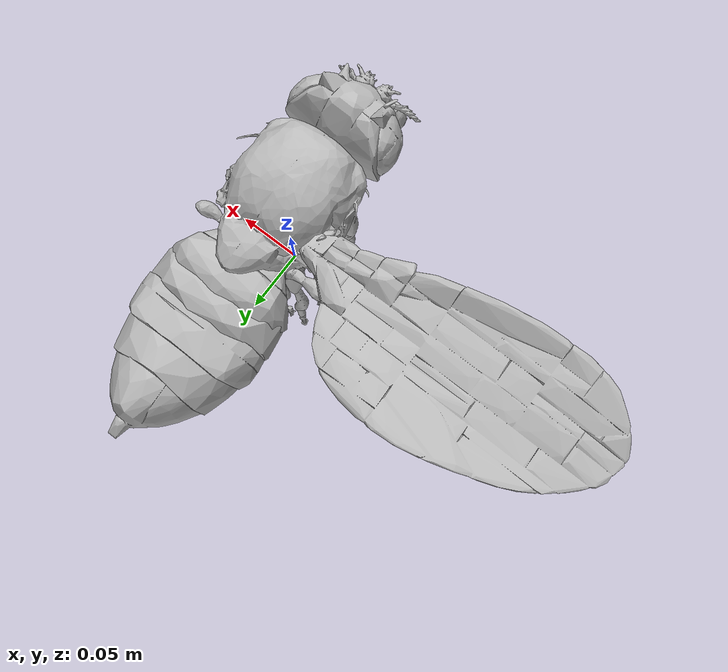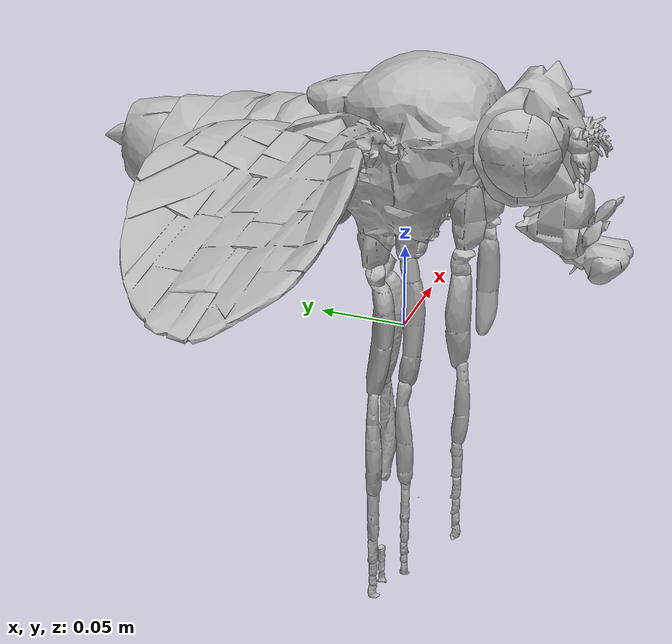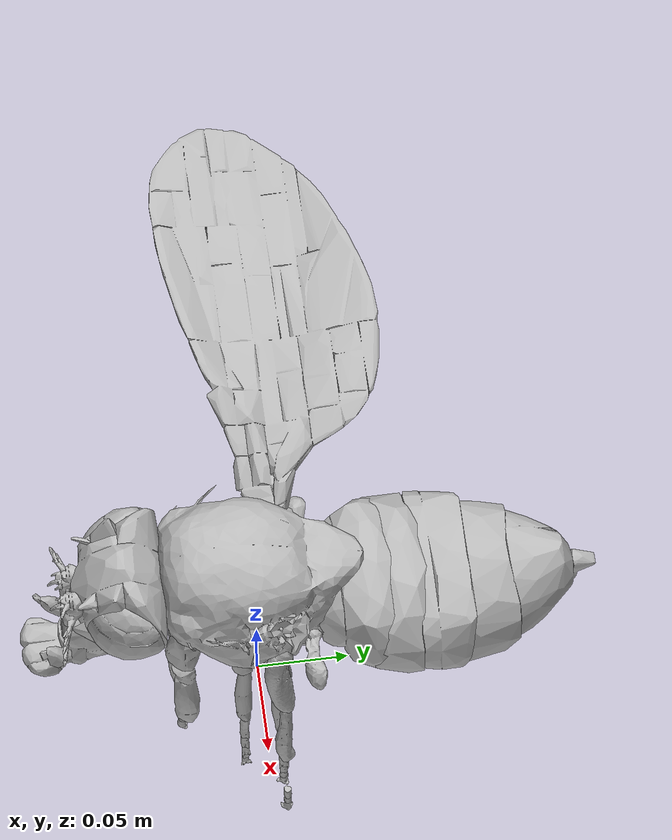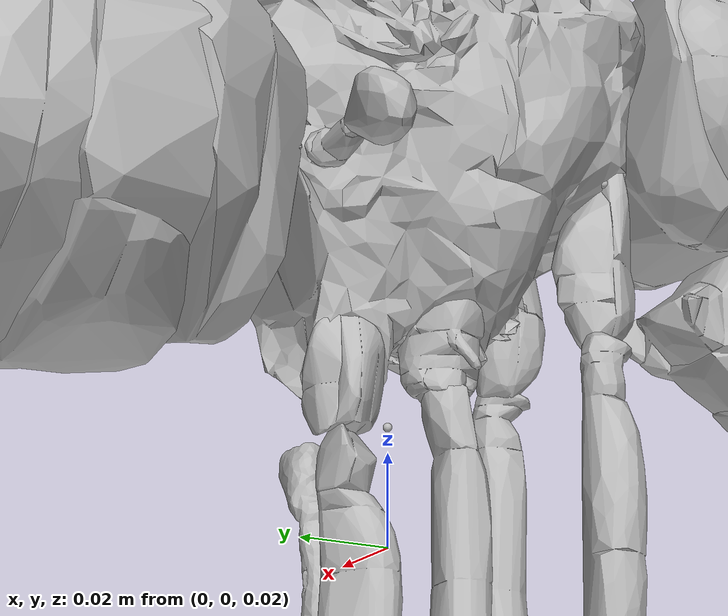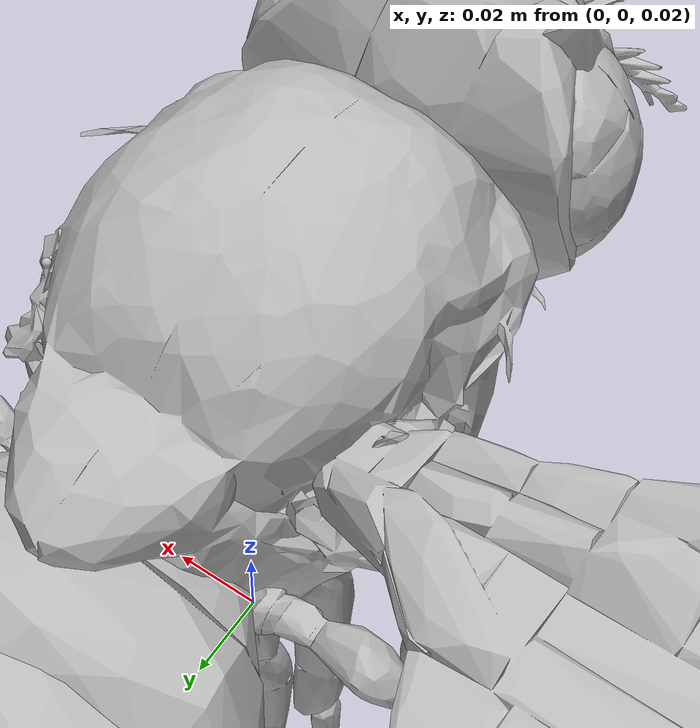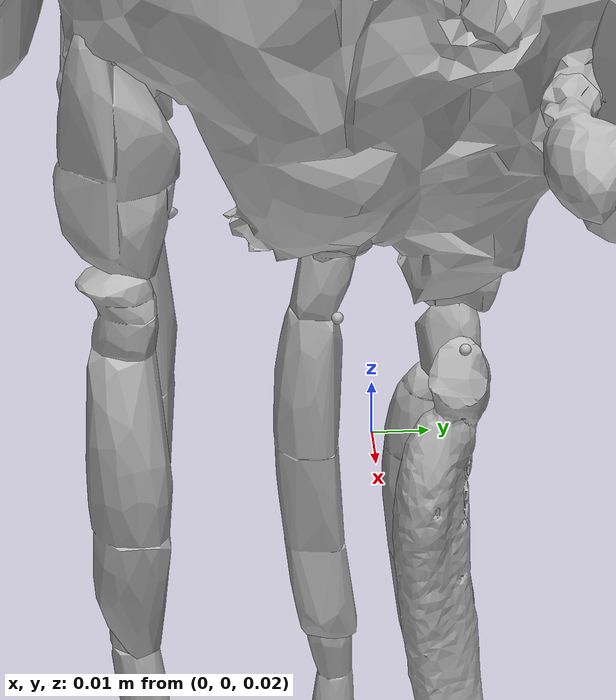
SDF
<?xml version="1.0" ?>
<sdf version="1.6">
  <model name="drosophila_100x">
    <link name="A1A2">
      <pose>-5.960464477539063e-08 0.030966036021709442 0.09105910360813141 0.0 0.0 0.0</pose>
      <inertial>
        <pose>-6.60141277691578e-06 0.021440143495774586 0.0070719728560120695 0.0 0.0 0.0</pose>
        <mass>0.13020633538809762</mass>
        <inertia>
          <ixx>4.381326077987316e-05</ixx>
          <ixy>4.124612233361468e-09</ixy>
          <ixz>1.9710935135202313e-08</ixz>
          <iyy>8.170736318802261e-05</iyy>
          <iyz>6.085974934573766e-06</iyz>
          <izz>6.507422986355485e-05</izz>
        </inertia>
      </inertial>
      <collision name="A1A2_collision">
        <geometry>
          <mesh>
            <uri>../meshes/stl/A1A2.stl</uri>
            <scale>1.0 1.0 1.0</scale>
          </mesh>
        </geometry>
      </collision>
      <visual name="A1A2_visual">
        <geometry>
          <mesh>
            <uri>../meshes/stl/A1A2.stl</uri>
            <scale>1.0 1.0 1.0</scale>
          </mesh>
        </geometry>
        <material/>
      </visual>
    </link>
    <link name="A3">
      <pose>-5.934527180784244e-08 0.06661386787891388 0.09098842740058899 0.0 0.0 0.0</pose>
      <inertial>
        <pose>-6.461729813035128e-06 0.005986951387270043 -0.0022718655874304364 0.0 0.0 0.0</pose>
        <mass>0.16258350012780076</mass>
        <inertia>
          <ixx>6.35055053450406e-05</ixx>
          <ixy>1.541722451084674e-09</ixy>
          <ixz>6.1850877052519354e-09</ixz>
          <iyy>0.00013665528284020776</iyy>
          <iyz>3.3156647239873862e-06</iyz>
          <izz>9.904359048119381e-05</izz>
        </inertia>
      </inertial>
      <collision name="A3_collision">
        <geometry>
          <mesh>
            <uri>../meshes/stl/A3.stl</uri>
            <scale>1.0 1.0 1.0</scale>
          </mesh>
        </geometry>
      </collision>
      <visual name="A3_visual">
        <geometry>
          <mesh>
            <uri>../meshes/stl/A3.stl</uri>
            <scale>1.0 1.0 1.0</scale>
          </mesh>
        </geometry>
        <material/>
      </visual>
    </link>
    <link name="A4">
      <pose>-5.840908912091436e-08 0.09037266671657562 0.09102427214384079 0.0 0.0 0.0</pose>
      <inertial>
        <pose>-2.9386016180563445e-06 0.0067161565440108295 -0.0017221664434351322 0.0 0.0 0.0</pose>
        <mass>0.14813264918700447</mass>
        <inertia>
          <ixx>4.948162026034623e-05</ixx>
          <ixy>3.5662990034681587e-09</ixy>
          <ixz>9.487554737298052e-10</ixz>
          <iyy>0.0001223037573136511</iyy>
          <iyz>2.440713242720652e-06</iyz>
          <izz>9.481390444935997e-05</izz>
        </inertia>
      </inertial>
      <collision name="A4_collision">
        <geometry>
          <mesh>
            <uri>../meshes/stl/A4.stl</uri>
            <scale>1.0 1.0 1.0</scale>
          </mesh>
        </geometry>
      </collision>
      <visual name="A4_visual">
        <geometry>
          <mesh>
            <uri>../meshes/stl/A4.stl</uri>
            <scale>1.0 1.0 1.0</scale>
          </mesh>
        </geometry>
        <material/>
      </visual>
    </link>
    <link name="A5">
      <pose>-5.768966104824358e-08 0.11180256307125092 0.09101486206054688 0.0 0.0 0.0</pose>
      <inertial>
        <pose>2.2301261838546264e-06 0.008342547108083787 -0.004064638742420903 0.0 0.0 0.0</pose>
        <mass>0.14739830635836168</mass>
        <inertia>
          <ixx>5.157013734526017e-05</ixx>
          <ixy>9.64835617060937e-09</ixy>
          <ixz>-1.7725652443046652e-08</ixz>
          <iyy>9.888661059284003e-05</iyy>
          <iyz>-3.8197497431134196e-07</iyz>
          <izz>7.683902516772778e-05</izz>
        </inertia>
      </inertial>
      <collision name="A5_collision">
        <geometry>
          <mesh>
            <uri>../meshes/stl/A5.stl</uri>
            <scale>1.0 1.0 1.0</scale>
          </mesh>
        </geometry>
      </collision>
      <visual name="A5_visual">
        <geometry>
          <mesh>
            <uri>../meshes/stl/A5.stl</uri>
            <scale>1.0 1.0 1.0</scale>
          </mesh>
        </geometry>
        <material/>
      </visual>
    </link>
    <link name="A6">
      <pose>-5.619395437861385e-08 0.13860782980918884 0.09106523543596268 0.0 0.0 0.0</pose>
      <inertial>
        <pose>1.044492970895423e-06 0.005388496834679199 -0.0034834605409008864 0.0 0.0 0.0</pose>
        <mass>0.09519384071698003</mass>
        <inertia>
          <ixx>2.9933248509655206e-05</ixx>
          <ixy>-1.16298963625115e-09</ixy>
          <ixz>6.403933716068139e-10</ixz>
          <iyy>3.901820816778398e-05</iyy>
          <iyz>7.560731335343763e-07</iyz>
          <izz>3.098151535655591e-05</izz>
        </inertia>
      </inertial>
      <collision name="A6_collision">
        <geometry>
          <mesh>
            <uri>../meshes/stl/A6.stl</uri>
            <scale>1.0 1.0 1.0</scale>
          </mesh>
        </geometry>
      </collision>
      <visual name="A6_visual">
        <geometry>
          <mesh>
            <uri>../meshes/stl/A6.stl</uri>
            <scale>1.0 1.0 1.0</scale>
          </mesh>
        </geometry>
        <material/>
      </visual>
    </link>
    <link name="Head">
      <pose>-5.960464477539063e-08 -0.049792952835559845 0.12107866257429123 0.0 0.0 0.0</pose>
      <inertial>
        <pose>-0.0012803619768014616 -0.020074989031441143 0.00474824061762323 0.0 0.0 0.0</pose>
        <mass>0.11613518173965927</mass>
        <inertia>
          <ixx>4.1859892321289714e-05</ixx>
          <ixy>-7.901226317174082e-07</ixy>
          <ixz>-2.8884091878857204e-07</ixz>
          <iyy>5.58801042201478e-05</iyy>
          <iyz>1.886422158705564e-06</iyz>
          <izz>4.391705652313935e-05</izz>
        </inertia>
      </inertial>
      <collision name="Head_collision">
        <geometry>
          <mesh>
            <uri>../meshes/stl/Head.stl</uri>
            <scale>1.0 1.0 1.0</scale>
          </mesh>
        </geometry>
      </collision>
      <visual name="Head_visual">
        <geometry>
          <mesh>
            <uri>../meshes/stl/Head.stl</uri>
            <scale>1.0 1.0 1.0</scale>
          </mesh>
        </geometry>
        <material/>
      </visual>
    </link>
    <link name="LAntenna">
      <pose>-0.006800519768148661 -0.09306174516677856 0.13498297333717346 0.0 0.0 0.0</pose>
      <inertial>
        <pose>-0.0013293016840823105 -0.005032582718190558 -0.010989321710342519 0.0 0.0 0.0</pose>
        <mass>0.002544729906096745</mass>
        <inertia>
          <ixx>1.4919088746722757e-07</ixx>
          <ixy>9.251915295125024e-09</ixy>
          <ixz>5.178598700413601e-09</ixz>
          <iyy>1.725904032300645e-07</iyy>
          <iyz>1.542062027850642e-08</iyz>
          <izz>7.120247658990056e-08</izz>
        </inertia>
      </inertial>
      <collision name="LAntenna_collision">
        <geometry>
          <mesh>
            <uri>../meshes/stl/LAntenna.stl</uri>
            <scale>1.0 1.0 1.0</scale>
          </mesh>
        </geometry>
      </collision>
      <visual name="LAntenna_visual">
        <geometry>
          <mesh>
            <uri>../meshes/stl/LAntenna.stl</uri>
            <scale>1.0 1.0 1.0</scale>
          </mesh>
        </geometry>
        <material/>
      </visual>
    </link>
    <link name="LEye">
      <pose>-5.960464477539063e-08 -0.07500004023313522 0.1299997717142105 0.0 0.0 0.0</pose>
      <inertial>
        <pose>-0.031758916341292125 0.0032918636628712582 -0.0030676929519103174 0.0 0.0 0.0</pose>
        <mass>0.011842625412682606</mass>
        <inertia>
          <ixx>2.334703896876576e-06</ixx>
          <ixy>-2.8964094809606157e-07</ixy>
          <ixz>-1.293673443350268e-07</ixz>
          <iyy>1.6886110780710643e-06</iyy>
          <iyz>1.7668054427303724e-07</iyz>
          <izz>1.121562852847439e-06</izz>
        </inertia>
      </inertial>
      <collision name="LEye_collision">
        <geometry>
          <mesh>
            <uri>../meshes/stl/LEye.stl</uri>
            <scale>1.0 1.0 1.0</scale>
          </mesh>
        </geometry>
      </collision>
      <visual name="LEye_visual">
        <geometry>
          <mesh>
            <uri>../meshes/stl/LEye.stl</uri>
            <scale>1.0 1.0 1.0</scale>
          </mesh>
        </geometry>
        <material/>
      </visual>
    </link>
    <link name="LFCoxa">
      <pose>-0.02162994258105755 -0.041307270526885986 0.10071428120136261 0.0 0.0 0.0</pose>
      <inertial>
        <pose>0.004021551406115924 -0.0004332004350006177 -0.018024884654787496 0.0 0.0 0.0</pose>
        <mass>0.00493369994515273</mass>
        <inertia>
          <ixx>5.213721452447612e-07</ixx>
          <ixy>2.5962892436397393e-09</ixy>
          <ixz>-7.0961383691175995e-09</ixz>
          <iyy>4.909620974537656e-07</iyy>
          <iyz>-2.5034810357152588e-08</iyz>
          <izz>1.2208634412155172e-07</izz>
        </inertia>
      </inertial>
      <collision name="LFCoxa_collision">
        <geometry>
          <mesh>
            <uri>../meshes/stl/LFCoxa.stl</uri>
            <scale>1.0 1.0 1.0</scale>
          </mesh>
        </geometry>
      </collision>
      <visual name="LFCoxa_visual">
        <geometry>
          <mesh>
            <uri>../meshes/stl/LFCoxa.stl</uri>
            <scale>1.0 1.0 1.0</scale>
          </mesh>
        </geometry>
        <material/>
      </visual>
    </link>
    <link name="LFCoxa_roll">
      <pose>-0.02162994258105755 -0.041307270526885986 0.10071428120136261 0.0 0.0 0.0</pose>
      <inertial>
        <pose>0.0 0.0 0.0 0.0 0.0 0.0</pose>
        <mass>0.0</mass>
        <inertia>
          <ixx>0.0</ixx>
          <ixy>0.0</ixy>
          <ixz>0.0</ixz>
          <iyy>0.0</iyy>
          <iyz>0.0</iyz>
          <izz>0.0</izz>
        </inertia>
      </inertial>
      <collision name="LFCoxa_roll_collision">
        <geometry>
          <sphere>
            <radius>0.001</radius>
          </sphere>
        </geometry>
      </collision>
      <visual name="LFCoxa_roll_visual">
        <geometry>
          <sphere>
            <radius>0.001</radius>
          </sphere>
        </geometry>
        <material/>
      </visual>
    </link>
    <link name="LFCoxa_yaw">
      <pose>-0.02162994258105755 -0.041307270526885986 0.10071428120136261 0.0 0.0 0.0</pose>
      <inertial>
        <pose>0.0 0.0 0.0 0.0 0.0 0.0</pose>
        <mass>0.0</mass>
        <inertia>
          <ixx>0.0</ixx>
          <ixy>0.0</ixy>
          <ixz>0.0</ixz>
          <iyy>0.0</iyy>
          <iyz>0.0</iyz>
          <izz>0.0</izz>
        </inertia>
      </inertial>
      <collision name="LFCoxa_yaw_collision">
        <geometry>
          <sphere>
            <radius>0.001</radius>
          </sphere>
        </geometry>
      </collision>
      <visual name="LFCoxa_yaw_visual">
        <geometry>
          <sphere>
            <radius>0.001</radius>
          </sphere>
        </geometry>
        <material/>
      </visual>
    </link>
    <link name="LFFemur">
      <pose>-0.0216140765696764 -0.0411619134247303 0.0654526874423027 0.0 0.0 0.0</pose>
      <inertial>
        <pose>-0.0015085238290117446 0.0014617126670147184 -0.03830016281509824 0.0 0.0 0.0</pose>
        <mass>0.0068674294081640065</mass>
        <inertia>
          <ixx>2.347142156773869e-06</ixx>
          <ixy>-5.136333898150057e-09</ixy>
          <ixz>-2.0181651265488044e-08</ixz>
          <iyy>2.355934607942084e-06</iyy>
          <iyz>3.2291283727061925e-09</iyz>
          <izz>1.2373362488654002e-07</izz>
        </inertia>
      </inertial>
      <collision name="LFFemur_collision">
        <geometry>
          <mesh>
            <uri>../meshes/stl/LFFemur.stl</uri>
            <scale>1.0 1.0 1.0</scale>
          </mesh>
        </geometry>
      </collision>
      <visual name="LFFemur_visual">
        <geometry>
          <mesh>
            <uri>../meshes/stl/LFFemur.stl</uri>
            <scale>1.0 1.0 1.0</scale>
          </mesh>
        </geometry>
        <material/>
      </visual>
    </link>
    <link name="LFFemur_roll">
      <pose>-0.0216140765696764 -0.0411619134247303 0.0654526874423027 0.0 0.0 0.0</pose>
      <inertial>
        <pose>0.0 0.0 0.0 0.0 0.0 0.0</pose>
        <mass>0.0</mass>
        <inertia>
          <ixx>0.0</ixx>
          <ixy>0.0</ixy>
          <ixz>0.0</ixz>
          <iyy>0.0</iyy>
          <iyz>0.0</iyz>
          <izz>0.0</izz>
        </inertia>
      </inertial>
      <collision name="LFFemur_roll_collision">
        <geometry>
          <sphere>
            <radius>0.001</radius>
          </sphere>
        </geometry>
      </collision>
      <visual name="LFFemur_roll_visual">
        <geometry>
          <sphere>
            <radius>0.001</radius>
          </sphere>
        </geometry>
        <material/>
      </visual>
    </link>
    <link name="LFTarsus1">
      <pose>-0.0217325147241354 -0.04115463048219681 -0.05691418796777725 0.0 0.0 0.0</pose>
      <inertial>
        <pose>0.0007753592371503444 0.0006146912475449463 -0.012335641668260363 0.0 0.0 0.0</pose>
        <mass>0.0005071727445685112</mass>
        <inertia>
          <ixx>2.2952845303979545e-08</ixx>
          <ixy>-5.754069290621259e-11</ixy>
          <ixz>-2.1243458938591237e-10</ixz>
          <iyy>2.287379528417514e-08</iyy>
          <iyz>7.303926200248354e-10</iyz>
          <izz>1.836408962892e-09</izz>
        </inertia>
      </inertial>
      <collision name="LFTarsus1_collision">
        <geometry>
          <mesh>
            <uri>../meshes/stl/LFTarsus1.stl</uri>
            <scale>1.0 1.0 1.0</scale>
          </mesh>
        </geometry>
      </collision>
      <visual name="LFTarsus1_visual">
        <geometry>
          <mesh>
            <uri>../meshes/stl/LFTarsus1.stl</uri>
            <scale>1.0 1.0 1.0</scale>
          </mesh>
        </geometry>
        <material/>
      </visual>
    </link>
    <link name="LFTarsus2">
      <pose>-0.021704107522964478 -0.04119134694337845 -0.07945730537176132 0.0 0.0 0.0</pose>
      <inertial>
        <pose>0.00033620913255235567 0.0003193351563735072 -0.008919907763296988 0.0 0.0 0.0</pose>
        <mass>0.00022847916197698317</mass>
        <inertia>
          <ixx>4.391152691367653e-09</ixx>
          <ixy>-3.998239880781822e-11</ixy>
          <ixz>-9.813553614141185e-12</ixz>
          <iyy>4.38527577313892e-09</iyy>
          <iyz>-1.917875515018473e-10</iyz>
          <izz>5.750901713817111e-10</izz>
        </inertia>
      </inertial>
      <collision name="LFTarsus2_collision">
        <geometry>
          <mesh>
            <uri>../meshes/stl/LFTarsus2.stl</uri>
            <scale>1.0 1.0 1.0</scale>
          </mesh>
        </geometry>
      </collision>
      <visual name="LFTarsus2_visual">
        <geometry>
          <mesh>
            <uri>../meshes/stl/LFTarsus2.stl</uri>
            <scale>1.0 1.0 1.0</scale>
          </mesh>
        </geometry>
        <material/>
      </visual>
    </link>
    <link name="LFTarsus3">
      <pose>-0.02173859067261219 -0.041141197085380554 -0.0948251336812973 0.0 0.0 0.0</pose>
      <inertial>
        <pose>0.00018402687113154594 0.00025023931725324746 -0.005933910956408003 0.0 0.0 0.0</pose>
        <mass>0.00012930751599850152</mass>
        <inertia>
          <ixx>1.1147952043068522e-09</ixx>
          <ixy>-1.4060246677610799e-11</ixy>
          <ixz>3.039260466338183e-11</ixz>
          <iyy>1.1122567845036611e-09</iyy>
          <iyz>-6.345042896921059e-11</iyz>
          <izz>2.782051892776527e-10</izz>
        </inertia>
      </inertial>
      <collision name="LFTarsus3_collision">
        <geometry>
          <mesh>
            <uri>../meshes/stl/LFTarsus3.stl</uri>
            <scale>1.0 1.0 1.0</scale>
          </mesh>
        </geometry>
      </collision>
      <visual name="LFTarsus3_visual">
        <geometry>
          <mesh>
            <uri>../meshes/stl/LFTarsus3.stl</uri>
            <scale>1.0 1.0 1.0</scale>
          </mesh>
        </geometry>
        <material/>
      </visual>
    </link>
    <link name="LFTarsus4">
      <pose>-0.021807702258229256 -0.04115293174982071 -0.10467547178268433 0.0 0.0 0.0</pose>
      <inertial>
        <pose>5.516182006013386e-05 6.575548532826896e-05 -0.005003968459085769 0.0 0.0 0.0</pose>
        <mass>0.00010113626261199664</mass>
        <inertia>
          <ixx>6.547232244911329e-10</ixx>
          <ixy>-9.639571756400195e-12</ixy>
          <ixz>1.613951249158464e-11</ixz>
          <iyy>6.509040913661884e-10</iyy>
          <iyz>-3.559760619259567e-11</iyz>
          <izz>1.9633855932095887e-10</izz>
        </inertia>
      </inertial>
      <collision name="LFTarsus4_collision">
        <geometry>
          <mesh>
            <uri>../meshes/stl/LFTarsus4.stl</uri>
            <scale>1.0 1.0 1.0</scale>
          </mesh>
        </geometry>
      </collision>
      <visual name="LFTarsus4_visual">
        <geometry>
          <mesh>
            <uri>../meshes/stl/LFTarsus4.stl</uri>
            <scale>1.0 1.0 1.0</scale>
          </mesh>
        </geometry>
        <material/>
      </visual>
    </link>
    <link name="LFTarsus5">
      <pose>-0.021823983639478683 -0.04115691035985947 -0.11337777227163315 0.0 0.0 0.0</pose>
      <inertial>
        <pose>8.60445484496291e-05 -9.418155381708948e-05 -0.0052033724170013704 0.0 0.0 0.0</pose>
        <mass>0.00012497671828143203</mass>
        <inertia>
          <ixx>1.031122512275193e-09</ixx>
          <ixy>-1.443957137192721e-11</ixy>
          <ixz>2.185064357958151e-11</ixz>
          <iyy>9.787690977678712e-10</iyy>
          <iyz>-7.135734618142614e-11</iyz>
          <izz>2.9474862291765306e-10</izz>
        </inertia>
      </inertial>
      <collision name="LFTarsus5_collision">
        <geometry>
          <mesh>
            <uri>../meshes/stl/LFTarsus5.stl</uri>
            <scale>1.0 1.0 1.0</scale>
          </mesh>
        </geometry>
      </collision>
      <visual name="LFTarsus5_visual">
        <geometry>
          <mesh>
            <uri>../meshes/stl/LFTarsus5.stl</uri>
            <scale>1.0 1.0 1.0</scale>
          </mesh>
        </geometry>
        <material/>
      </visual>
    </link>
    <link name="LFTibia">
      <pose>-0.021675260737538338 -0.041148945689201355 -0.0050722286105155945 0.0 0.0 0.0</pose>
      <inertial>
        <pose>0.00013390671784539786 -0.0009915698512157074 -0.029303735124132743 0.0 0.0 0.0</pose>
        <mass>0.0022571726525388637</mass>
        <inertia>
          <ixx>4.7426268916559163e-07</ixx>
          <ixy>1.3119624544062321e-09</ixy>
          <ixz>-1.8347556631087063e-08</ixz>
          <iyy>4.72948688254796e-07</iyy>
          <iyz>-1.6231735196800503e-08</iyz>
          <izz>1.8757160089103232e-08</izz>
        </inertia>
      </inertial>
      <collision name="LFTibia_collision">
        <geometry>
          <mesh>
            <uri>../meshes/stl/LFTibia.stl</uri>
            <scale>1.0 1.0 1.0</scale>
          </mesh>
        </geometry>
      </collision>
      <visual name="LFTibia_visual">
        <geometry>
          <mesh>
            <uri>../meshes/stl/LFTibia.stl</uri>
            <scale>1.0 1.0 1.0</scale>
          </mesh>
        </geometry>
        <material/>
      </visual>
    </link>
    <link name="LHCoxa">
      <pose>-0.008699516765773296 0.0147719606757164 0.06072309985756874 0.0 0.0 0.0</pose>
      <inertial>
        <pose>-0.002085729293361976 0.0003725980565486208 -0.010104028900283907 0.0 0.0 0.0</pose>
        <mass>0.0027968492344924273</mass>
        <inertia>
          <ixx>1.2442876339281293e-07</ixx>
          <ixy>-1.4219429692390606e-09</ixy>
          <ixz>-1.96182913612205e-08</ixz>
          <iyy>1.1608153431545319e-07</iyy>
          <iyz>-2.227507769330273e-09</iyz>
          <izz>7.632940052189791e-08</izz>
        </inertia>
      </inertial>
      <collision name="LHCoxa_collision">
        <geometry>
          <mesh>
            <uri>../meshes/stl/LHCoxa.stl</uri>
            <scale>1.0 1.0 1.0</scale>
          </mesh>
        </geometry>
      </collision>
      <visual name="LHCoxa_visual">
        <geometry>
          <mesh>
            <uri>../meshes/stl/LHCoxa.stl</uri>
            <scale>1.0 1.0 1.0</scale>
          </mesh>
        </geometry>
        <material/>
      </visual>
    </link>
    <link name="LHCoxa_roll">
      <pose>-0.008699516765773296 0.0147719606757164 0.06072309985756874 0.0 0.0 0.0</pose>
      <inertial>
        <pose>0.0 0.0 0.0 0.0 0.0 0.0</pose>
        <mass>0.0</mass>
        <inertia>
          <ixx>0.0</ixx>
          <ixy>0.0</ixy>
          <ixz>0.0</ixz>
          <iyy>0.0</iyy>
          <iyz>0.0</iyz>
          <izz>0.0</izz>
        </inertia>
      </inertial>
      <collision name="LHCoxa_roll_collision">
        <geometry>
          <sphere>
            <radius>0.001</radius>
          </sphere>
        </geometry>
      </collision>
      <visual name="LHCoxa_roll_visual">
        <geometry>
          <sphere>
            <radius>0.001</radius>
          </sphere>
        </geometry>
        <material/>
      </visual>
    </link>
    <link name="LHCoxa_yaw">
      <pose>-0.008699516765773296 0.0147719606757164 0.06072309985756874 0.0 0.0 0.0</pose>
      <inertial>
        <pose>0.0 0.0 0.0 0.0 0.0 0.0</pose>
        <mass>0.0</mass>
        <inertia>
          <ixx>0.0</ixx>
          <ixy>0.0</ixy>
          <ixz>0.0</ixz>
          <iyy>0.0</iyy>
          <iyz>0.0</iyz>
          <izz>0.0</izz>
        </inertia>
      </inertial>
      <collision name="LHCoxa_yaw_collision">
        <geometry>
          <sphere>
            <radius>0.001</radius>
          </sphere>
        </geometry>
      </collision>
      <visual name="LHCoxa_yaw_visual">
        <geometry>
          <sphere>
            <radius>0.001</radius>
          </sphere>
        </geometry>
        <material/>
      </visual>
    </link>
    <link name="LHFemur">
      <pose>-0.008657796308398247 0.014779784716665745 0.04078115522861481 0.0 0.0 0.0</pose>
      <inertial>
        <pose>0.0018144142266171834 -0.0033165677232437256 -0.04390959726208214 0.0 0.0 0.0</pose>
        <mass>0.009549740734344846</mass>
        <inertia>
          <ixx>4.503612571777631e-06</ixx>
          <ixy>2.9620934061144648e-08</ixy>
          <ixz>-8.825927449708312e-08</ixz>
          <iyy>4.5034285983705555e-06</iyy>
          <iyz>-7.492838300038931e-08</iyz>
          <izz>2.327493668518702e-07</izz>
        </inertia>
      </inertial>
      <collision name="LHFemur_collision">
        <geometry>
          <mesh>
            <uri>../meshes/stl/LHFemur.stl</uri>
            <scale>1.0 1.0 1.0</scale>
          </mesh>
        </geometry>
      </collision>
      <visual name="LHFemur_visual">
        <geometry>
          <mesh>
            <uri>../meshes/stl/LHFemur.stl</uri>
            <scale>1.0 1.0 1.0</scale>
          </mesh>
        </geometry>
        <material/>
      </visual>
    </link>
    <link name="LHFemur_roll">
      <pose>-0.008657796308398247 0.014779784716665745 0.04078115522861481 0.0 0.0 0.0</pose>
      <inertial>
        <pose>0.0 0.0 0.0 0.0 0.0 0.0</pose>
        <mass>0.0</mass>
        <inertia>
          <ixx>0.0</ixx>
          <ixy>0.0</ixy>
          <ixz>0.0</ixz>
          <iyy>0.0</iyy>
          <iyz>0.0</iyz>
          <izz>0.0</izz>
        </inertia>
      </inertial>
      <collision name="LHFemur_roll_collision">
        <geometry>
          <sphere>
            <radius>0.001</radius>
          </sphere>
        </geometry>
      </collision>
      <visual name="LHFemur_roll_visual">
        <geometry>
          <sphere>
            <radius>0.001</radius>
          </sphere>
        </geometry>
        <material/>
      </visual>
    </link>
    <link name="LHTarsus1">
      <pose>-0.008607779629528522 0.014797641895711422 -0.11129769682884216 0.0 0.0 0.0</pose>
      <inertial>
        <pose>0.0003258804553850013 0.0004109842660948211 -0.016765790684785006 0.0 0.0 0.0</pose>
        <mass>0.0011385448507272617</mass>
        <inertia>
          <ixx>1.1940775207672404e-07</ixx>
          <ixy>4.953817922930203e-10</ixy>
          <ixz>1.3589560132147223e-09</ixz>
          <iyy>1.1952085880538046e-07</iyy>
          <iyz>4.302435778076122e-10</iyz>
          <izz>6.341828700288815e-09</izz>
        </inertia>
      </inertial>
      <collision name="LHTarsus1_collision">
        <geometry>
          <mesh>
            <uri>../meshes/stl/LHTarsus1.stl</uri>
            <scale>1.0 1.0 1.0</scale>
          </mesh>
        </geometry>
      </collision>
      <visual name="LHTarsus1_visual">
        <geometry>
          <mesh>
            <uri>../meshes/stl/LHTarsus1.stl</uri>
            <scale>1.0 1.0 1.0</scale>
          </mesh>
        </geometry>
        <material/>
      </visual>
    </link>
    <link name="LHTarsus2">
      <pose>-0.00861196219921112 0.014772334136068821 -0.14657245576381683 0.0 0.0 0.0</pose>
      <inertial>
        <pose>0.00011539268040219153 0.000388679553993479 -0.009134700526599116 0.0 0.0 0.0</pose>
        <mass>0.0003837167273584865</mass>
        <inertia>
          <ixx>1.0715816968829604e-08</ixx>
          <ixy>-4.135655338619783e-11</ixy>
          <ixz>-2.5451298488458017e-10</ixz>
          <iyy>1.068702469237023e-08</iyy>
          <iyz>-1.6262234148408502e-10</iyz>
          <izz>1.3590908400829124e-09</izz>
        </inertia>
      </inertial>
      <collision name="LHTarsus2_collision">
        <geometry>
          <mesh>
            <uri>../meshes/stl/LHTarsus2.stl</uri>
            <scale>1.0 1.0 1.0</scale>
          </mesh>
        </geometry>
      </collision>
      <visual name="LHTarsus2_visual">
        <geometry>
          <mesh>
            <uri>../meshes/stl/LHTarsus2.stl</uri>
            <scale>1.0 1.0 1.0</scale>
          </mesh>
        </geometry>
        <material/>
      </visual>
    </link>
    <link name="LHTarsus3">
      <pose>-0.008640987798571587 0.014749557711184025 -0.16407814621925354 0.0 0.0 0.0</pose>
      <inertial>
        <pose>0.00040997719559940495 0.00027753040220472635 -0.004873177693157315 0.0 0.0 0.0</pose>
        <mass>0.00014755584940983314</mass>
        <inertia>
          <ixx>1.3666597947449725e-09</ixx>
          <ixy>-1.6844943979713642e-11</ixy>
          <ixz>-2.381170142129718e-11</ixz>
          <iyy>1.355324427830512e-09</iyy>
          <iyz>-6.0375794297221765e-12</iyz>
          <izz>3.635486068303056e-10</izz>
        </inertia>
      </inertial>
      <collision name="LHTarsus3_collision">
        <geometry>
          <mesh>
            <uri>../meshes/stl/LHTarsus3.stl</uri>
            <scale>1.0 1.0 1.0</scale>
          </mesh>
        </geometry>
      </collision>
      <visual name="LHTarsus3_visual">
        <geometry>
          <mesh>
            <uri>../meshes/stl/LHTarsus3.stl</uri>
            <scale>1.0 1.0 1.0</scale>
          </mesh>
        </geometry>
        <material/>
      </visual>
    </link>
    <link name="LHTarsus4">
      <pose>-0.008602237328886986 0.01480130385607481 -0.17374934256076813 0.0 0.0 0.0</pose>
      <inertial>
        <pose>0.0002987344236334343 0.00028860910561438437 -0.004006913326471853 0.0 0.0 0.0</pose>
        <mass>9.833019821769069e-05</mass>
        <inertia>
          <ixx>5.502965882863764e-10</ixx>
          <ixy>-1.2474720078818844e-11</ixy>
          <ixz>-2.2835389552401727e-11</ixz>
          <iyy>5.519249643360152e-10</iyy>
          <iyz>2.1329446721903623e-11</iyz>
          <izz>2.119614821844786e-10</izz>
        </inertia>
      </inertial>
      <collision name="LHTarsus4_collision">
        <geometry>
          <mesh>
            <uri>../meshes/stl/LHTarsus4.stl</uri>
            <scale>1.0 1.0 1.0</scale>
          </mesh>
        </geometry>
      </collision>
      <visual name="LHTarsus4_visual">
        <geometry>
          <mesh>
            <uri>../meshes/stl/LHTarsus4.stl</uri>
            <scale>1.0 1.0 1.0</scale>
          </mesh>
        </geometry>
        <material/>
      </visual>
    </link>
    <link name="LHTarsus5">
      <pose>-0.008632366545498371 0.014765641652047634 -0.18107977509498596 0.0 0.0 0.0</pose>
      <inertial>
        <pose>0.00010174989758372729 0.000363544004371024 -0.005257307636417405 0.0 0.0 0.0</pose>
        <mass>0.00013603730315311477</mass>
        <inertia>
          <ixx>1.1505969648033715e-09</ixx>
          <ixy>-3.2216487484858896e-11</ixy>
          <ixz>-1.5789007834132823e-11</ixz>
          <iyy>1.114479876688536e-09</iyy>
          <iyz>4.3576508053681495e-11</iyz>
          <izz>3.709590749174205e-10</izz>
        </inertia>
      </inertial>
      <collision name="LHTarsus5_collision">
        <geometry>
          <mesh>
            <uri>../meshes/stl/LHTarsus5.stl</uri>
            <scale>1.0 1.0 1.0</scale>
          </mesh>
        </geometry>
      </collision>
      <visual name="LHTarsus5_visual">
        <geometry>
          <mesh>
            <uri>../meshes/stl/LHTarsus5.stl</uri>
            <scale>1.0 1.0 1.0</scale>
          </mesh>
        </geometry>
        <material/>
      </visual>
    </link>
    <link name="LHTibia">
      <pose>-0.008673958480358124 0.014771521091461182 -0.0428512766957283 0.0 0.0 0.0</pose>
      <inertial>
        <pose>-0.0027041548800393837 -0.0007578744939256431 -0.04177044623236621 0.0 0.0 0.0</pose>
        <mass>0.003678070694258461</mass>
        <inertia>
          <ixx>1.1725223376851997e-06</ixx>
          <ixy>1.4216683716176142e-09</ixy>
          <ixz>-6.176852741020778e-08</ixz>
          <iyy>1.1810868924984267e-06</iyy>
          <iyz>-1.2124083159957592e-09</iyz>
          <izz>4.239389640513967e-08</izz>
        </inertia>
      </inertial>
      <collision name="LHTibia_collision">
        <geometry>
          <mesh>
            <uri>../meshes/stl/LHTibia.stl</uri>
            <scale>1.0 1.0 1.0</scale>
          </mesh>
        </geometry>
      </collision>
      <visual name="LHTibia_visual">
        <geometry>
          <mesh>
            <uri>../meshes/stl/LHTibia.stl</uri>
            <scale>1.0 1.0 1.0</scale>
          </mesh>
        </geometry>
        <material/>
      </visual>
    </link>
    <link name="LHaltere">
      <pose>-0.021355997771024704 0.025897085666656494 0.09370222687721252 0.0 0.0 0.0</pose>
      <inertial>
        <pose>-0.020605148326773605 0.0007622043546424694 -0.0002901905022523117 0.0 0.0 0.0</pose>
        <mass>0.0020444374976513863</mass>
        <inertia>
          <ixx>2.848598061703332e-08</ixx>
          <ixy>8.010218301565769e-11</ixy>
          <ixz>9.281424504214993e-10</ixz>
          <iyy>2.0181485858985463e-07</iyy>
          <iyz>1.7412423082136197e-09</iyz>
          <izz>1.976703879093075e-07</izz>
        </inertia>
      </inertial>
      <collision name="LHaltere_collision">
        <geometry>
          <mesh>
            <uri>../meshes/stl/LHaltere.stl</uri>
            <scale>1.0 1.0 1.0</scale>
          </mesh>
        </geometry>
      </collision>
      <visual name="LHaltere_visual">
        <geometry>
          <mesh>
            <uri>../meshes/stl/LHaltere.stl</uri>
            <scale>1.0 1.0 1.0</scale>
          </mesh>
        </geometry>
        <material/>
      </visual>
    </link>
    <link name="LHaltere_roll">
      <pose>-0.021355997771024704 0.025897085666656494 0.09370222687721252 0.0 0.0 0.0</pose>
      <inertial>
        <pose>0.0 0.0 0.0 0.0 0.0 0.0</pose>
        <mass>0.0</mass>
        <inertia>
          <ixx>0.0</ixx>
          <ixy>0.0</ixy>
          <ixz>0.0</ixz>
          <iyy>0.0</iyy>
          <iyz>0.0</iyz>
          <izz>0.0</izz>
        </inertia>
      </inertial>
      <collision name="LHaltere_roll_collision">
        <geometry>
          <sphere>
            <radius>0.001</radius>
          </sphere>
        </geometry>
      </collision>
      <visual name="LHaltere_roll_visual">
        <geometry>
          <sphere>
            <radius>0.001</radius>
          </sphere>
        </geometry>
        <material/>
      </visual>
    </link>
    <link name="LHaltere_yaw">
      <pose>-0.021355997771024704 0.025897085666656494 0.09370222687721252 0.0 0.0 0.0</pose>
      <inertial>
        <pose>0.0 0.0 0.0 0.0 0.0 0.0</pose>
        <mass>0.0</mass>
        <inertia>
          <ixx>0.0</ixx>
          <ixy>0.0</ixy>
          <ixz>0.0</ixz>
          <iyy>0.0</iyy>
          <iyz>0.0</iyz>
          <izz>0.0</izz>
        </inertia>
      </inertial>
      <collision name="LHaltere_yaw_collision">
        <geometry>
          <sphere>
            <radius>0.001</radius>
          </sphere>
        </geometry>
      </collision>
      <visual name="LHaltere_yaw_visual">
        <geometry>
          <sphere>
            <radius>0.001</radius>
          </sphere>
        </geometry>
        <material/>
      </visual>
    </link>
    <link name="LMCoxa">
      <pose>-0.0124903479591012 -0.006767649203538895 0.0679856538772583 0.0 0.0 0.0</pose>
      <inertial>
        <pose>-0.000488565006719788 0.00013440210980868633 -0.007883668545955607 0.0 0.0 0.0</pose>
        <mass>0.0028321424332875505</mass>
        <inertia>
          <ixx>1.292452812681875e-07</ixx>
          <ixy>-4.4924235649555556e-10</ixy>
          <ixz>-3.8576925139103127e-08</ixz>
          <iyy>1.3867826608816933e-07</iyy>
          <iyz>-3.816991501246567e-09</iyz>
          <izz>9.052248911232482e-08</izz>
        </inertia>
      </inertial>
      <collision name="LMCoxa_collision">
        <geometry>
          <mesh>
            <uri>../meshes/stl/LMCoxa.stl</uri>
            <scale>1.0 1.0 1.0</scale>
          </mesh>
        </geometry>
      </collision>
      <visual name="LMCoxa_visual">
        <geometry>
          <mesh>
            <uri>../meshes/stl/LMCoxa.stl</uri>
            <scale>1.0 1.0 1.0</scale>
          </mesh>
        </geometry>
        <material/>
      </visual>
    </link>
    <link name="LMCoxa_roll">
      <pose>-0.0124903479591012 -0.006767649203538895 0.0679856538772583 0.0 0.0 0.0</pose>
      <inertial>
        <pose>0.0 0.0 0.0 0.0 0.0 0.0</pose>
        <mass>0.0</mass>
        <inertia>
          <ixx>0.0</ixx>
          <ixy>0.0</ixy>
          <ixz>0.0</ixz>
          <iyy>0.0</iyy>
          <iyz>0.0</iyz>
          <izz>0.0</izz>
        </inertia>
      </inertial>
      <collision name="LMCoxa_roll_collision">
        <geometry>
          <sphere>
            <radius>0.001</radius>
          </sphere>
        </geometry>
      </collision>
      <visual name="LMCoxa_roll_visual">
        <geometry>
          <sphere>
            <radius>0.001</radius>
          </sphere>
        </geometry>
        <material/>
      </visual>
    </link>
    <link name="LMCoxa_yaw">
      <pose>-0.0124903479591012 -0.006767649203538895 0.0679856538772583 0.0 0.0 0.0</pose>
      <inertial>
        <pose>0.0 0.0 0.0 0.0 0.0 0.0</pose>
        <mass>0.0</mass>
        <inertia>
          <ixx>0.0</ixx>
          <ixy>0.0</ixy>
          <ixz>0.0</ixz>
          <iyy>0.0</iyy>
          <iyz>0.0</iyz>
          <izz>0.0</izz>
        </inertia>
      </inertial>
      <collision name="LMCoxa_yaw_collision">
        <geometry>
          <sphere>
            <radius>0.001</radius>
          </sphere>
        </geometry>
      </collision>
      <visual name="LMCoxa_yaw_visual">
        <geometry>
          <sphere>
            <radius>0.001</radius>
          </sphere>
        </geometry>
        <material/>
      </visual>
    </link>
    <link name="LMFemur">
      <pose>-0.012511943466961384 -0.006746102590113878 0.04984075576066971 0.0 0.0 0.0</pose>
      <inertial>
        <pose>-0.00019034471892417516 -0.002351268477092087 -0.040513357942080094 0.0 0.0 0.0</pose>
        <mass>0.00707250669313801</mass>
        <inertia>
          <ixx>3.5232681896487285e-06</ixx>
          <ixy>-8.662826389116525e-10</ixy>
          <ixz>-3.2597731254104036e-08</ixz>
          <iyy>3.5222141727544528e-06</iyy>
          <iyz>-1.2497318206341416e-08</iyz>
          <izz>1.1716840743767099e-07</izz>
        </inertia>
      </inertial>
      <collision name="LMFemur_collision">
        <geometry>
          <mesh>
            <uri>../meshes/stl/LMFemur.stl</uri>
            <scale>1.0 1.0 1.0</scale>
          </mesh>
        </geometry>
      </collision>
      <visual name="LMFemur_visual">
        <geometry>
          <mesh>
            <uri>../meshes/stl/LMFemur.stl</uri>
            <scale>1.0 1.0 1.0</scale>
          </mesh>
        </geometry>
        <material/>
      </visual>
    </link>
    <link name="LMFemur_roll">
      <pose>-0.012511943466961384 -0.006746102590113878 0.04984075576066971 0.0 0.0 0.0</pose>
      <inertial>
        <pose>0.0 0.0 0.0 0.0 0.0 0.0</pose>
        <mass>0.0</mass>
        <inertia>
          <ixx>0.0</ixx>
          <ixy>0.0</ixy>
          <ixz>0.0</ixz>
          <iyy>0.0</iyy>
          <iyz>0.0</iyz>
          <izz>0.0</izz>
        </inertia>
      </inertial>
      <collision name="LMFemur_roll_collision">
        <geometry>
          <sphere>
            <radius>0.001</radius>
          </sphere>
        </geometry>
      </collision>
      <visual name="LMFemur_roll_visual">
        <geometry>
          <sphere>
            <radius>0.001</radius>
          </sphere>
        </geometry>
        <material/>
      </visual>
    </link>
    <link name="LMTarsus1">
      <pose>-0.012434279546141624 -0.006634240970015526 -0.09526075422763824 0.0 0.0 0.0</pose>
      <inertial>
        <pose>0.0003064078797770667 0.00010572775667967473 -0.015359220207039469 0.0 0.0 0.0</pose>
        <mass>0.0005725323552152925</mass>
        <inertia>
          <ixx>4.1126690709533204e-08</ixx>
          <ixy>9.649547508115664e-11</ixy>
          <ixz>2.5408930793501607e-09</ixz>
          <iyy>4.143499032656478e-08</iyy>
          <iyz>8.400878162973956e-10</iyz>
          <izz>2.0588666247307623e-09</izz>
        </inertia>
      </inertial>
      <collision name="LMTarsus1_collision">
        <geometry>
          <mesh>
            <uri>../meshes/stl/LMTarsus1.stl</uri>
            <scale>1.0 1.0 1.0</scale>
          </mesh>
        </geometry>
      </collision>
      <visual name="LMTarsus1_visual">
        <geometry>
          <mesh>
            <uri>../meshes/stl/LMTarsus1.stl</uri>
            <scale>1.0 1.0 1.0</scale>
          </mesh>
        </geometry>
        <material/>
      </visual>
    </link>
    <link name="LMTarsus2">
      <pose>-0.012482634745538235 -0.00669208075851202 -0.12425801157951355 0.0 0.0 0.0</pose>
      <inertial>
        <pose>-8.876343433799286e-05 8.015963208555351e-05 -0.008344985468383387 0.0 0.0 0.0</pose>
        <mass>0.00025683336881689937</mass>
        <inertia>
          <ixx>5.221404744612318e-09</ixx>
          <ixy>-9.409782185804766e-12</ixy>
          <ixz>5.333585552873769e-11</ixz>
          <iyy>5.262812507433424e-09</iyy>
          <iyz>1.004442863068708e-10</iyz>
          <izz>6.98554867624274e-10</izz>
        </inertia>
      </inertial>
      <collision name="LMTarsus2_collision">
        <geometry>
          <mesh>
            <uri>../meshes/stl/LMTarsus2.stl</uri>
            <scale>1.0 1.0 1.0</scale>
          </mesh>
        </geometry>
      </collision>
      <visual name="LMTarsus2_visual">
        <geometry>
          <mesh>
            <uri>../meshes/stl/LMTarsus2.stl</uri>
            <scale>1.0 1.0 1.0</scale>
          </mesh>
        </geometry>
        <material/>
      </visual>
    </link>
    <link name="LMTarsus3">
      <pose>-0.012472659349441528 -0.006695592775940895 -0.14027342200279236 0.0 0.0 0.0</pose>
      <inertial>
        <pose>-0.00028039716907236716 0.0003349726696149423 -0.004787056679650857 0.0 0.0 0.0</pose>
        <mass>0.00012834121432298885</mass>
        <inertia>
          <ixx>1.00436926435763e-09</ixx>
          <ixy>-6.697761077154022e-12</ixy>
          <ixz>-6.761685166705012e-11</ixz>
          <iyy>1.0318048523965904e-09</iyy>
          <iyz>-1.815808873334538e-11</iyz>
          <izz>3.12255883405537e-10</izz>
        </inertia>
      </inertial>
      <collision name="LMTarsus3_collision">
        <geometry>
          <mesh>
            <uri>../meshes/stl/LMTarsus3.stl</uri>
            <scale>1.0 1.0 1.0</scale>
          </mesh>
        </geometry>
      </collision>
      <visual name="LMTarsus3_visual">
        <geometry>
          <mesh>
            <uri>../meshes/stl/LMTarsus3.stl</uri>
            <scale>1.0 1.0 1.0</scale>
          </mesh>
        </geometry>
        <material/>
      </visual>
    </link>
    <link name="LMTarsus4">
      <pose>-0.012451604008674622 -0.00664735259488225 -0.14951704442501068 0.0 0.0 0.0</pose>
      <inertial>
        <pose>-0.00014021108252089043 0.00016964930762413145 -0.00326319412895851 0.0 0.0 0.0</pose>
        <mass>7.467449508125764e-05</mass>
        <inertia>
          <ixx>2.7483355183606025e-10</ixx>
          <ixy>-3.128501569162579e-12</ixy>
          <ixz>-1.8835860667306418e-11</ixz>
          <iyy>2.8958679709377763e-10</iyy>
          <iyz>8.19347285248712e-12</iyz>
          <izz>1.57972406878782e-10</izz>
        </inertia>
      </inertial>
      <collision name="LMTarsus4_collision">
        <geometry>
          <mesh>
            <uri>../meshes/stl/LMTarsus4.stl</uri>
            <scale>1.0 1.0 1.0</scale>
          </mesh>
        </geometry>
      </collision>
      <visual name="LMTarsus4_visual">
        <geometry>
          <mesh>
            <uri>../meshes/stl/LMTarsus4.stl</uri>
            <scale>1.0 1.0 1.0</scale>
          </mesh>
        </geometry>
        <material/>
      </visual>
    </link>
    <link name="LMTarsus5">
      <pose>-0.012466147541999817 -0.006808344274759293 -0.1558893471956253 0.0 0.0 0.0</pose>
      <inertial>
        <pose>-0.0002869359921430059 0.00012241696128082632 -0.004333021295008068 0.0 0.0 0.0</pose>
        <mass>0.00012437319115254702</mass>
        <inertia>
          <ixx>9.977545578786778e-10</ixx>
          <ixy>3.0780093493394266e-12</ixy>
          <ixz>-7.865105571332082e-11</ixz>
          <iyy>1.0529058942847748e-09</iyy>
          <iyz>2.3374151357324402e-12</iyz>
          <izz>3.0089702207846384e-10</izz>
        </inertia>
      </inertial>
      <collision name="LMTarsus5_collision">
        <geometry>
          <mesh>
            <uri>../meshes/stl/LMTarsus5.stl</uri>
            <scale>1.0 1.0 1.0</scale>
          </mesh>
        </geometry>
      </collision>
      <visual name="LMTarsus5_visual">
        <geometry>
          <mesh>
            <uri>../meshes/stl/LMTarsus5.stl</uri>
            <scale>1.0 1.0 1.0</scale>
          </mesh>
        </geometry>
        <material/>
      </visual>
    </link>
    <link name="LMTibia">
      <pose>-0.012517733499407768 -0.006648960057646036 -0.028527237474918365 0.0 0.0 0.0</pose>
      <inertial>
        <pose>-0.0025413476929807785 0.00039871856064358397 -0.03738085521306658 0.0 0.0 0.0</pose>
        <mass>0.00312049409835183</mass>
        <inertia>
          <ixx>1.1556166028161049e-06</ixx>
          <ixy>-2.5110180224534096e-09</ixy>
          <ixz>-6.382043554863699e-08</ixz>
          <iyy>1.1567618158211306e-06</iyy>
          <iyz>1.8291492093555407e-08</iyz>
          <izz>2.8869294552535615e-08</izz>
        </inertia>
      </inertial>
      <collision name="LMTibia_collision">
        <geometry>
          <mesh>
            <uri>../meshes/stl/LMTibia.stl</uri>
            <scale>1.0 1.0 1.0</scale>
          </mesh>
        </geometry>
      </collision>
      <visual name="LMTibia_visual">
        <geometry>
          <mesh>
            <uri>../meshes/stl/LMTibia.stl</uri>
            <scale>1.0 1.0 1.0</scale>
          </mesh>
        </geometry>
        <material/>
      </visual>
    </link>
    <link name="LWing">
      <pose>-0.03698383644223213 0.009160667657852173 0.13241985440254211 0.0 0.0 0.0</pose>
      <inertial>
        <pose>-0.09942472095858121 0.01025026338231106 0.007636318283653762 0.0 0.0 0.0</pose>
        <mass>0.03664079301230228</mass>
        <inertia>
          <ixx>2.4948110696057808e-05</ixx>
          <ixy>5.5888372320093675e-06</ixy>
          <ixz>2.1343325141090043e-06</ixz>
          <iyy>0.00013828109937744863</iyy>
          <iyz>3.6453134394521883e-07</iyz>
          <izz>0.0001609725348296115</izz>
        </inertia>
      </inertial>
      <collision name="LWing_collision">
        <geometry>
          <mesh>
            <uri>../meshes/stl/LWing.stl</uri>
            <scale>1.0 1.0 1.0</scale>
          </mesh>
        </geometry>
      </collision>
      <visual name="LWing_visual">
        <geometry>
          <mesh>
            <uri>../meshes/stl/LWing.stl</uri>
            <scale>1.0 1.0 1.0</scale>
          </mesh>
        </geometry>
        <material/>
      </visual>
    </link>
    <link name="LWing_roll">
      <pose>-0.03698383644223213 0.009160667657852173 0.13241985440254211 0.0 0.0 0.0</pose>
      <inertial>
        <pose>0.0 0.0 0.0 0.0 0.0 0.0</pose>
        <mass>0.0</mass>
        <inertia>
          <ixx>0.0</ixx>
          <ixy>0.0</ixy>
          <ixz>0.0</ixz>
          <iyy>0.0</iyy>
          <iyz>0.0</iyz>
          <izz>0.0</izz>
        </inertia>
      </inertial>
      <collision name="LWing_roll_collision">
        <geometry>
          <sphere>
            <radius>0.001</radius>
          </sphere>
        </geometry>
      </collision>
      <visual name="LWing_roll_visual">
        <geometry>
          <sphere>
            <radius>0.001</radius>
          </sphere>
        </geometry>
        <material/>
      </visual>
    </link>
    <link name="LWing_yaw">
      <pose>-0.03698383644223213 0.009160667657852173 0.13241985440254211 0.0 0.0 0.0</pose>
      <inertial>
        <pose>0.0 0.0 0.0 0.0 0.0 0.0</pose>
        <mass>0.0</mass>
        <inertia>
          <ixx>0.0</ixx>
          <ixy>0.0</ixy>
          <ixz>0.0</ixz>
          <iyy>0.0</iyy>
          <iyz>0.0</iyz>
          <izz>0.0</izz>
        </inertia>
      </inertial>
      <collision name="LWing_yaw_collision">
        <geometry>
          <sphere>
            <radius>0.001</radius>
          </sphere>
        </geometry>
      </collision>
      <visual name="LWing_yaw_visual">
        <geometry>
          <sphere>
            <radius>0.001</radius>
          </sphere>
        </geometry>
        <material/>
      </visual>
    </link>
    <link name="Labellum">
      <pose>2.345762914046645e-05 -0.09131887555122375 0.06270226836204529 0.0 0.0 0.0</pose>
      <inertial>
        <pose>0.0004712144199847123 -0.019963913529345012 -0.0006670810102943538 0.0 0.0 0.0</pose>
        <mass>0.00993475018565492</mass>
        <inertia>
          <ixx>8.406493089899029e-07</ixx>
          <ixy>-2.5550539775918226e-09</ixy>
          <ixz>4.427143866547032e-09</ixz>
          <iyy>7.011431696274997e-07</iyy>
          <iyz>-1.1544789158548692e-09</iyz>
          <izz>1.1462160533174146e-06</izz>
        </inertia>
      </inertial>
      <collision name="Labellum_collision">
        <geometry>
          <mesh>
            <uri>../meshes/stl/Labellum.stl</uri>
            <scale>1.0 1.0 1.0</scale>
          </mesh>
        </geometry>
      </collision>
      <visual name="Labellum_visual">
        <geometry>
          <mesh>
            <uri>../meshes/stl/Labellum.stl</uri>
            <scale>1.0 1.0 1.0</scale>
          </mesh>
        </geometry>
        <material/>
      </visual>
    </link>
    <link name="Proboscis">
      <pose>6.79532895446755e-05 -0.09129957109689713 0.09984789788722992 0.0 0.0 0.0</pose>
      <inertial>
        <pose>-2.3155502003198655e-05 -9.38072812098964e-06 -0.01813619620308267 0.0 0.0 0.0</pose>
        <mass>0.02236480725478538</mass>
        <inertia>
          <ixx>3.510018138425648e-06</ixx>
          <ixy>-3.540905844473321e-09</ixy>
          <ixz>1.6592074274312787e-09</ixz>
          <iyy>3.0643642668406175e-06</iyy>
          <iyz>-2.6592140667679057e-08</iyz>
          <izz>3.016136318134015e-06</izz>
        </inertia>
      </inertial>
      <collision name="Proboscis_collision">
        <geometry>
          <mesh>
            <uri>../meshes/stl/Proboscis.stl</uri>
            <scale>1.0 1.0 1.0</scale>
          </mesh>
        </geometry>
      </collision>
      <visual name="Proboscis_visual">
        <geometry>
          <mesh>
            <uri>../meshes/stl/Proboscis.stl</uri>
            <scale>1.0 1.0 1.0</scale>
          </mesh>
        </geometry>
        <material/>
      </visual>
    </link>
    <link name="RAntenna">
      <pose>0.006690086331218481 -0.09306374937295914 0.135030135512352 0.0 0.0 0.0</pose>
      <inertial>
        <pose>0.0013140373955789568 -0.005035037661166296 -0.010989984300560524 0.0 0.0 0.0</pose>
        <mass>0.002544733327051085</mass>
        <inertia>
          <ixx>1.4910584860502956e-07</ixx>
          <ixy>-9.074368833843477e-09</ixy>
          <ixz>-5.177601693664291e-09</ixz>
          <iyy>1.7279790980803113e-07</iyy>
          <iyz>1.5095916730665696e-08</iyz>
          <izz>7.109332958243586e-08</izz>
        </inertia>
      </inertial>
      <collision name="RAntenna_collision">
        <geometry>
          <mesh>
            <uri>../meshes/stl/RAntenna.stl</uri>
            <scale>1.0 1.0 1.0</scale>
          </mesh>
        </geometry>
      </collision>
      <visual name="RAntenna_visual">
        <geometry>
          <mesh>
            <uri>../meshes/stl/RAntenna.stl</uri>
            <scale>1.0 1.0 1.0</scale>
          </mesh>
        </geometry>
        <material/>
      </visual>
    </link>
    <link name="REye">
      <pose>-5.960464477539063e-08 -0.07500004023313522 0.1299997717142105 0.0 0.0 0.0</pose>
      <inertial>
        <pose>0.030097617345959535 0.002706964060349753 -0.002379388265269219 0.0 0.0 0.0</pose>
        <mass>0.013653715414556372</mass>
        <inertia>
          <ixx>2.558481727602674e-06</ixx>
          <ixy>3.435191901851373e-07</ixy>
          <ixz>8.41619989331661e-08</ixz>
          <iyy>1.8844418108242712e-06</iyy>
          <iyz>1.1752665803139789e-07</iyz>
          <izz>1.2665346344878013e-06</izz>
        </inertia>
      </inertial>
      <collision name="REye_collision">
        <geometry>
          <mesh>
            <uri>../meshes/stl/REye.stl</uri>
            <scale>1.0 1.0 1.0</scale>
          </mesh>
        </geometry>
      </collision>
      <visual name="REye_visual">
        <geometry>
          <mesh>
            <uri>../meshes/stl/REye.stl</uri>
            <scale>1.0 1.0 1.0</scale>
          </mesh>
        </geometry>
        <material/>
      </visual>
    </link>
    <link name="RFCoxa">
      <pose>0.021629853174090385 -0.04130726307630539 0.10071435570716858 0.0 0.0 0.0</pose>
      <inertial>
        <pose>-0.0014158940597103736 -0.0003931559768268574 -0.017979106469072206 0.0 0.0 0.0</pose>
        <mass>0.004933708978897873</mass>
        <inertia>
          <ixx>5.213495432127117e-07</ixx>
          <ixy>-2.7102534006620916e-09</ixy>
          <ixz>7.470447370463702e-09</ixz>
          <iyy>4.911761217928834e-07</iyy>
          <iyz>-2.361260452400765e-08</iyz>
          <izz>1.2191310328181836e-07</izz>
        </inertia>
      </inertial>
      <collision name="RFCoxa_collision">
        <geometry>
          <mesh>
            <uri>../meshes/stl/RFCoxa.stl</uri>
            <scale>1.0 1.0 1.0</scale>
          </mesh>
        </geometry>
      </collision>
      <visual name="RFCoxa_visual">
        <geometry>
          <mesh>
            <uri>../meshes/stl/RFCoxa.stl</uri>
            <scale>1.0 1.0 1.0</scale>
          </mesh>
        </geometry>
        <material/>
      </visual>
    </link>
    <link name="RFCoxa_roll">
      <pose>0.021629853174090385 -0.04130726307630539 0.10071435570716858 0.0 0.0 0.0</pose>
      <inertial>
        <pose>0.0 0.0 0.0 0.0 0.0 0.0</pose>
        <mass>0.0</mass>
        <inertia>
          <ixx>0.0</ixx>
          <ixy>0.0</ixy>
          <ixz>0.0</ixz>
          <iyy>0.0</iyy>
          <iyz>0.0</iyz>
          <izz>0.0</izz>
        </inertia>
      </inertial>
      <collision name="RFCoxa_roll_collision">
        <geometry>
          <sphere>
            <radius>0.001</radius>
          </sphere>
        </geometry>
      </collision>
      <visual name="RFCoxa_roll_visual">
        <geometry>
          <sphere>
            <radius>0.001</radius>
          </sphere>
        </geometry>
        <material/>
      </visual>
    </link>
    <link name="RFCoxa_yaw">
      <pose>0.021629853174090385 -0.04130726307630539 0.10071435570716858 0.0 0.0 0.0</pose>
      <inertial>
        <pose>0.0 0.0 0.0 0.0 0.0 0.0</pose>
        <mass>0.0</mass>
        <inertia>
          <ixx>0.0</ixx>
          <ixy>0.0</ixy>
          <ixz>0.0</ixz>
          <iyy>0.0</iyy>
          <iyz>0.0</iyz>
          <izz>0.0</izz>
        </inertia>
      </inertial>
      <collision name="RFCoxa_yaw_collision">
        <geometry>
          <sphere>
            <radius>0.001</radius>
          </sphere>
        </geometry>
      </collision>
      <visual name="RFCoxa_yaw_visual">
        <geometry>
          <sphere>
            <radius>0.001</radius>
          </sphere>
        </geometry>
        <material/>
      </visual>
    </link>
    <link name="RFFemur">
      <pose>0.021590309217572212 -0.04129485785961151 0.0654524713754654 0.0 0.0 0.0</pose>
      <inertial>
        <pose>0.0031497889009300195 -7.73297310563545e-05 -0.03746950856891247 0.0 0.0 0.0</pose>
        <mass>0.006867432724706132</mass>
        <inertia>
          <ixx>2.346571587089987e-06</ixx>
          <ixy>5.139766037345132e-09</ixy>
          <ixz>3.9575238205122784e-08</ixz>
          <iyy>2.3559891326078892e-06</iyy>
          <iyz>4.380889610098921e-09</iyz>
          <izz>1.2425926628022993e-07</izz>
        </inertia>
      </inertial>
      <collision name="RFFemur_collision">
        <geometry>
          <mesh>
            <uri>../meshes/stl/RFFemur.stl</uri>
            <scale>1.0 1.0 1.0</scale>
          </mesh>
        </geometry>
      </collision>
      <visual name="RFFemur_visual">
        <geometry>
          <mesh>
            <uri>../meshes/stl/RFFemur.stl</uri>
            <scale>1.0 1.0 1.0</scale>
          </mesh>
        </geometry>
        <material/>
      </visual>
    </link>
    <link name="RFFemur_roll">
      <pose>0.021590309217572212 -0.04129485785961151 0.0654524713754654 0.0 0.0 0.0</pose>
      <inertial>
        <pose>0.0 0.0 0.0 0.0 0.0 0.0</pose>
        <mass>0.0</mass>
        <inertia>
          <ixx>0.0</ixx>
          <ixy>0.0</ixy>
          <ixz>0.0</ixz>
          <iyy>0.0</iyy>
          <iyz>0.0</iyz>
          <izz>0.0</izz>
        </inertia>
      </inertial>
      <collision name="RFFemur_roll_collision">
        <geometry>
          <sphere>
            <radius>0.001</radius>
          </sphere>
        </geometry>
      </collision>
      <visual name="RFFemur_roll_visual">
        <geometry>
          <sphere>
            <radius>0.001</radius>
          </sphere>
        </geometry>
        <material/>
      </visual>
    </link>
    <link name="RFTarsus1">
      <pose>0.021673033013939857 -0.04132082313299179 -0.056911323219537735 0.0 0.0 0.0</pose>
      <inertial>
        <pose>0.00014551999117642817 9.408157526226551e-05 -0.012081178370882992 0.0 0.0 0.0</pose>
        <mass>0.0005071733265009364</mass>
        <inertia>
          <ixx>2.294110495337767e-08</ixx>
          <ixy>6.707103897418924e-11</ixy>
          <ixz>5.215592401595416e-10</ixz>
          <iyy>2.2879459632728192e-08</iyy>
          <iyz>6.60120822843132e-10</iyz>
          <izz>1.8425696667319276e-09</izz>
        </inertia>
      </inertial>
      <collision name="RFTarsus1_collision">
        <geometry>
          <mesh>
            <uri>../meshes/stl/RFTarsus1.stl</uri>
            <scale>1.0 1.0 1.0</scale>
          </mesh>
        </geometry>
      </collision>
      <visual name="RFTarsus1_visual">
        <geometry>
          <mesh>
            <uri>../meshes/stl/RFTarsus1.stl</uri>
            <scale>1.0 1.0 1.0</scale>
          </mesh>
        </geometry>
        <material/>
      </visual>
    </link>
    <link name="RFTarsus2">
      <pose>0.021639585494995117 -0.04131960868835449 -0.07946331053972244 0.0 0.0 0.0</pose>
      <inertial>
        <pose>0.0003393730992770075 -5.178471201620363e-05 -0.008606674050264676 0.0 0.0 0.0</pose>
        <mass>0.00022847914581884058</mass>
        <inertia>
          <ixx>4.389553115125496e-09</ixx>
          <ixy>3.801624324690399e-11</ixy>
          <ixz>5.170711173541343e-11</ixz>
          <iyy>4.387646560175508e-09</iyy>
          <iyz>-1.7726667973644443e-10</iyz>
          <izz>5.74318514433698e-10</izz>
        </inertia>
      </inertial>
      <collision name="RFTarsus2_collision">
        <geometry>
          <mesh>
            <uri>../meshes/stl/RFTarsus2.stl</uri>
            <scale>1.0 1.0 1.0</scale>
          </mesh>
        </geometry>
      </collision>
      <visual name="RFTarsus2_visual">
        <geometry>
          <mesh>
            <uri>../meshes/stl/RFTarsus2.stl</uri>
            <scale>1.0 1.0 1.0</scale>
          </mesh>
        </geometry>
        <material/>
      </visual>
    </link>
    <link name="RFTarsus3">
      <pose>0.02165445126593113 -0.04135359823703766 -0.09483037889003754 0.0 0.0 0.0</pose>
      <inertial>
        <pose>0.00019754479549307293 6.855120720067165e-06 -0.005755610631269033 0.0 0.0 0.0</pose>
        <mass>0.00012930754287827621</mass>
        <inertia>
          <ixx>1.1156228589257619e-09</ixx>
          <ixy>1.164929577830008e-11</ixy>
          <ixz>1.0762155499903522e-12</ixz>
          <iyy>1.1100280825373853e-09</iyy>
          <iyz>-7.857235577063411e-11</iyz>
          <izz>2.7960688604878815e-10</izz>
        </inertia>
      </inertial>
      <collision name="RFTarsus3_collision">
        <geometry>
          <mesh>
            <uri>../meshes/stl/RFTarsus3.stl</uri>
            <scale>1.0 1.0 1.0</scale>
          </mesh>
        </geometry>
      </collision>
      <visual name="RFTarsus3_visual">
        <geometry>
          <mesh>
            <uri>../meshes/stl/RFTarsus3.stl</uri>
            <scale>1.0 1.0 1.0</scale>
          </mesh>
        </geometry>
        <material/>
      </visual>
    </link>
    <link name="RFTarsus4">
      <pose>0.02164452150464058 -0.0413220040500164 -0.1045285239815712 0.0 0.0 0.0</pose>
      <inertial>
        <pose>0.00022700161724606468 1.1428192164221233e-05 -0.005037512784936681 0.0 0.0 0.0</pose>
        <mass>0.00010113632950391928</mass>
        <inertia>
          <ixx>6.548755596267789e-10</ixx>
          <ixy>9.248281881229051e-12</ixy>
          <ixz>-1.150875299030361e-11</ixz>
          <iyy>6.512802283402128e-10</iyy>
          <iyz>-3.409478707947233e-11</iyz>
          <izz>1.9581217754223972e-10</izz>
        </inertia>
      </inertial>
      <collision name="RFTarsus4_collision">
        <geometry>
          <mesh>
            <uri>../meshes/stl/RFTarsus4.stl</uri>
            <scale>1.0 1.0 1.0</scale>
          </mesh>
        </geometry>
      </collision>
      <visual name="RFTarsus4_visual">
        <geometry>
          <mesh>
            <uri>../meshes/stl/RFTarsus4.stl</uri>
            <scale>1.0 1.0 1.0</scale>
          </mesh>
        </geometry>
        <material/>
      </visual>
    </link>
    <link name="RFTarsus5">
      <pose>0.021725278347730637 -0.04137614369392395 -0.11322999745607376 0.0 0.0 0.0</pose>
      <inertial>
        <pose>-5.4960166612520644e-05 -4.792709884470202e-05 -0.005221589041560994 0.0 0.0 0.0</pose>
        <mass>0.00012497680048782046</mass>
        <inertia>
          <ixx>1.0316605906679188e-09</ixx>
          <ixy>1.3249094066075627e-11</ixy>
          <ixz>-4.987433578554218e-12</ixz>
          <iyy>9.702345102437924e-10</iyy>
          <iyz>-1.0464520704986605e-10</iyz>
          <izz>3.0274571884538457e-10</izz>
        </inertia>
      </inertial>
      <collision name="RFTarsus5_collision">
        <geometry>
          <mesh>
            <uri>../meshes/stl/RFTarsus5.stl</uri>
            <scale>1.0 1.0 1.0</scale>
          </mesh>
        </geometry>
      </collision>
      <visual name="RFTarsus5_visual">
        <geometry>
          <mesh>
            <uri>../meshes/stl/RFTarsus5.stl</uri>
            <scale>1.0 1.0 1.0</scale>
          </mesh>
        </geometry>
        <material/>
      </visual>
    </link>
    <link name="RFTibia">
      <pose>0.021663974970579147 -0.041316140443086624 -0.005072437226772308 0.0 0.0 0.0</pose>
      <inertial>
        <pose>0.0009080041684202958 -0.001295556755338096 -0.029395855477796707 0.0 0.0 0.0</pose>
        <mass>0.002257666315504129</mass>
        <inertia>
          <ixx>4.744908416593753e-07</ixx>
          <ixy>-1.368853148619553e-09</ixy>
          <ixz>1.76579876644666e-08</ixz>
          <iyy>4.729089255233603e-07</iyy>
          <iyz>-1.872474750271873e-08</iyz>
          <izz>1.8903238742928257e-08</izz>
        </inertia>
      </inertial>
      <collision name="RFTibia_collision">
        <geometry>
          <mesh>
            <uri>../meshes/stl/RFTibia.stl</uri>
            <scale>1.0 1.0 1.0</scale>
          </mesh>
        </geometry>
      </collision>
      <visual name="RFTibia_visual">
        <geometry>
          <mesh>
            <uri>../meshes/stl/RFTibia.stl</uri>
            <scale>1.0 1.0 1.0</scale>
          </mesh>
        </geometry>
        <material/>
      </visual>
    </link>
    <link name="RHCoxa">
      <pose>0.008699396625161171 0.014771946705877781 0.06072309985756874 0.0 0.0 0.0</pose>
      <inertial>
        <pose>0.0020954518888179146 0.0003820206377970326 -0.01010142255197682 0.0 0.0 0.0</pose>
        <mass>0.0027968483888566676</mass>
        <inertia>
          <ixx>1.2446474121148643e-07</ixx>
          <ixy>1.4067120552485313e-09</ixy>
          <ixz>1.9573732212713837e-08</ixz>
          <iyy>1.1607418827462112e-07</iyy>
          <iyz>-2.2685330015454533e-09</iyz>
          <izz>7.629850433285029e-08</izz>
        </inertia>
      </inertial>
      <collision name="RHCoxa_collision">
        <geometry>
          <mesh>
            <uri>../meshes/stl/RHCoxa.stl</uri>
            <scale>1.0 1.0 1.0</scale>
          </mesh>
        </geometry>
      </collision>
      <visual name="RHCoxa_visual">
        <geometry>
          <mesh>
            <uri>../meshes/stl/RHCoxa.stl</uri>
            <scale>1.0 1.0 1.0</scale>
          </mesh>
        </geometry>
        <material/>
      </visual>
    </link>
    <link name="RHCoxa_roll">
      <pose>0.008699396625161171 0.014771946705877781 0.06072309985756874 0.0 0.0 0.0</pose>
      <inertial>
        <pose>0.0 0.0 0.0 0.0 0.0 0.0</pose>
        <mass>0.0</mass>
        <inertia>
          <ixx>0.0</ixx>
          <ixy>0.0</ixy>
          <ixz>0.0</ixz>
          <iyy>0.0</iyy>
          <iyz>0.0</iyz>
          <izz>0.0</izz>
        </inertia>
      </inertial>
      <collision name="RHCoxa_roll_collision">
        <geometry>
          <sphere>
            <radius>0.001</radius>
          </sphere>
        </geometry>
      </collision>
      <visual name="RHCoxa_roll_visual">
        <geometry>
          <sphere>
            <radius>0.001</radius>
          </sphere>
        </geometry>
        <material/>
      </visual>
    </link>
    <link name="RHCoxa_yaw">
      <pose>0.008699396625161171 0.014771946705877781 0.06072309985756874 0.0 0.0 0.0</pose>
      <inertial>
        <pose>0.0 0.0 0.0 0.0 0.0 0.0</pose>
        <mass>0.0</mass>
        <inertia>
          <ixx>0.0</ixx>
          <ixy>0.0</ixy>
          <ixz>0.0</ixz>
          <iyy>0.0</iyy>
          <iyz>0.0</iyz>
          <izz>0.0</izz>
        </inertia>
      </inertial>
      <collision name="RHCoxa_yaw_collision">
        <geometry>
          <sphere>
            <radius>0.001</radius>
          </sphere>
        </geometry>
      </collision>
      <visual name="RHCoxa_yaw_visual">
        <geometry>
          <sphere>
            <radius>0.001</radius>
          </sphere>
        </geometry>
        <material/>
      </visual>
    </link>
    <link name="RHFemur">
      <pose>0.00867681484669447 0.014799416996538639 0.04078114032745361 0.0 0.0 0.0</pose>
      <inertial>
        <pose>-0.0018456253458032203 -0.0033173436706512047 -0.04390826505110377 0.0 0.0 0.0</pose>
        <mass>0.009549745532888843</mass>
        <inertia>
          <ixx>4.503568735783207e-06</ixx>
          <ixy>-2.966196901401424e-08</ixy>
          <ixz>9.08565945026782e-08</ixz>
          <iyy>4.503375211003071e-06</iyy>
          <iyz>-7.47355172818208e-08</iyz>
          <izz>2.3285232367313023e-07</izz>
        </inertia>
      </inertial>
      <collision name="RHFemur_collision">
        <geometry>
          <mesh>
            <uri>../meshes/stl/RHFemur.stl</uri>
            <scale>1.0 1.0 1.0</scale>
          </mesh>
        </geometry>
      </collision>
      <visual name="RHFemur_visual">
        <geometry>
          <mesh>
            <uri>../meshes/stl/RHFemur.stl</uri>
            <scale>1.0 1.0 1.0</scale>
          </mesh>
        </geometry>
        <material/>
      </visual>
    </link>
    <link name="RHFemur_roll">
      <pose>0.00867681484669447 0.014799416996538639 0.04078114032745361 0.0 0.0 0.0</pose>
      <inertial>
        <pose>0.0 0.0 0.0 0.0 0.0 0.0</pose>
        <mass>0.0</mass>
        <inertia>
          <ixx>0.0</ixx>
          <ixy>0.0</ixy>
          <ixz>0.0</ixz>
          <iyy>0.0</iyy>
          <iyz>0.0</iyz>
          <izz>0.0</izz>
        </inertia>
      </inertial>
      <collision name="RHFemur_roll_collision">
        <geometry>
          <sphere>
            <radius>0.001</radius>
          </sphere>
        </geometry>
      </collision>
      <visual name="RHFemur_roll_visual">
        <geometry>
          <sphere>
            <radius>0.001</radius>
          </sphere>
        </geometry>
        <material/>
      </visual>
    </link>
    <link name="RHTarsus1">
      <pose>0.00857723131775856 0.014759830199182034 -0.11129770427942276 0.0 0.0 0.0</pose>
      <inertial>
        <pose>-3.8455029903327675e-05 0.0005334370147638097 -0.016765621216522603 0.0 0.0 0.0</pose>
        <mass>0.0011385366253231395</mass>
        <inertia>
          <ixx>1.1986190928988546e-07</ixx>
          <ixy>-2.9292908118885647e-10</ixy>
          <ixz>-1.1928061065032401e-09</ixz>
          <iyy>1.1905939923854205e-07</iyy>
          <iyz>9.621756138466251e-10</iyz>
          <izz>6.344586911624052e-09</izz>
        </inertia>
      </inertial>
      <collision name="RHTarsus1_collision">
        <geometry>
          <mesh>
            <uri>../meshes/stl/RHTarsus1.stl</uri>
            <scale>1.0 1.0 1.0</scale>
          </mesh>
        </geometry>
      </collision>
      <visual name="RHTarsus1_visual">
        <geometry>
          <mesh>
            <uri>../meshes/stl/RHTarsus1.stl</uri>
            <scale>1.0 1.0 1.0</scale>
          </mesh>
        </geometry>
        <material/>
      </visual>
    </link>
    <link name="RHTarsus2">
      <pose>0.008641784079372883 0.014765683561563492 -0.14657239615917206 0.0 0.0 0.0</pose>
      <inertial>
        <pose>1.7040100664156253e-05 0.00041478073049473714 -0.009134280884184246 0.0 0.0 0.0</pose>
        <mass>0.000383717377357771</mass>
        <inertia>
          <ixx>1.0673817135581235e-08</ixx>
          <ixy>3.3680430466356574e-11</ixy>
          <ixz>2.1142030474824158e-10</ixz>
          <iyy>1.0725793998175705e-08</iyy>
          <iyz>-2.7824441333974375e-10</iyz>
          <izz>1.362390629270579e-09</izz>
        </inertia>
      </inertial>
      <collision name="RHTarsus2_collision">
        <geometry>
          <mesh>
            <uri>../meshes/stl/RHTarsus2.stl</uri>
            <scale>1.0 1.0 1.0</scale>
          </mesh>
        </geometry>
      </collision>
      <visual name="RHTarsus2_visual">
        <geometry>
          <mesh>
            <uri>../meshes/stl/RHTarsus2.stl</uri>
            <scale>1.0 1.0 1.0</scale>
          </mesh>
        </geometry>
        <material/>
      </visual>
    </link>
    <link name="RHTarsus3">
      <pose>0.008545194752514362 0.014763754792511463 -0.16407787799835205 0.0 0.0 0.0</pose>
      <inertial>
        <pose>-0.0001642521273130942 0.0004124441944976054 -0.004878074593802166 0.0 0.0 0.0</pose>
        <mass>0.00014755601891240422</mass>
        <inertia>
          <ixx>1.3495166543402786e-09</ixx>
          <ixy>1.3571267129081555e-11</ixy>
          <ixz>6.96879471386353e-12</ixz>
          <iyy>1.3729195578985633e-09</iyy>
          <iyz>-1.0213010665637616e-11</iyz>
          <izz>3.6310297042841154e-10</izz>
        </inertia>
      </inertial>
      <collision name="RHTarsus3_collision">
        <geometry>
          <mesh>
            <uri>../meshes/stl/RHTarsus3.stl</uri>
            <scale>1.0 1.0 1.0</scale>
          </mesh>
        </geometry>
      </collision>
      <visual name="RHTarsus3_visual">
        <geometry>
          <mesh>
            <uri>../meshes/stl/RHTarsus3.stl</uri>
            <scale>1.0 1.0 1.0</scale>
          </mesh>
        </geometry>
        <material/>
      </visual>
    </link>
    <link name="RHTarsus4">
      <pose>0.008640971966087818 0.014763089828193188 -0.17374883592128754 0.0 0.0 0.0</pose>
      <inertial>
        <pose>-0.00016520721628027454 0.0004099303167755065 -0.004004128386836757 0.0 0.0 0.0</pose>
        <mass>9.833040379602674e-05</mass>
        <inertia>
          <ixx>5.40579035468636e-10</ixx>
          <ixy>7.079506950903073e-12</ixy>
          <ixz>3.150494002672522e-11</ixz>
          <iyy>5.614228116286736e-10</iyy>
          <iyz>7.542885891135664e-12</iyz>
          <izz>2.1218500500014543e-10</izz>
        </inertia>
      </inertial>
      <collision name="RHTarsus4_collision">
        <geometry>
          <mesh>
            <uri>../meshes/stl/RHTarsus4.stl</uri>
            <scale>1.0 1.0 1.0</scale>
          </mesh>
        </geometry>
      </collision>
      <visual name="RHTarsus4_visual">
        <geometry>
          <mesh>
            <uri>../meshes/stl/RHTarsus4.stl</uri>
            <scale>1.0 1.0 1.0</scale>
          </mesh>
        </geometry>
        <material/>
      </visual>
    </link>
    <link name="RHTarsus5">
      <pose>0.008615629747509956 0.014755907468497753 -0.18107935786247253 0.0 0.0 0.0</pose>
      <inertial>
        <pose>2.7550561328148424e-05 0.00034333185225996794 -0.005259511312980976 0.0 0.0 0.0</pose>
        <mass>0.00013603737216280094</mass>
        <inertia>
          <ixx>1.1218624537524224e-09</ixx>
          <ixy>3.57600115578373e-11</ixy>
          <ixz>3.408352320906445e-11</ixz>
          <iyy>1.1425409784150736e-09</iyy>
          <iyz>3.8469768501016265e-11</iyz>
          <izz>3.7163592826630775e-10</izz>
        </inertia>
      </inertial>
      <collision name="RHTarsus5_collision">
        <geometry>
          <mesh>
            <uri>../meshes/stl/RHTarsus5.stl</uri>
            <scale>1.0 1.0 1.0</scale>
          </mesh>
        </geometry>
      </collision>
      <visual name="RHTarsus5_visual">
        <geometry>
          <mesh>
            <uri>../meshes/stl/RHTarsus5.stl</uri>
            <scale>1.0 1.0 1.0</scale>
          </mesh>
        </geometry>
        <material/>
      </visual>
    </link>
    <link name="RHTibia">
      <pose>0.008640495128929615 0.01478584110736847 -0.04285129904747009 0.0 0.0 0.0</pose>
      <inertial>
        <pose>0.0024643857994131706 -0.001382142611202153 -0.04176923196840837 0.0 0.0 0.0</pose>
        <mass>0.0036780722619137473</mass>
        <inertia>
          <ixx>1.1735589144939641e-06</ixx>
          <ixy>-3.084648837439861e-09</ixy>
          <ixz>6.002173072466198e-08</ixz>
          <iyy>1.180071985598996e-06</iyy>
          <iyz>-1.3852039092082498e-08</iyz>
          <izz>4.237401979106237e-08</izz>
        </inertia>
      </inertial>
      <collision name="RHTibia_collision">
        <geometry>
          <mesh>
            <uri>../meshes/stl/RHTibia.stl</uri>
            <scale>1.0 1.0 1.0</scale>
          </mesh>
        </geometry>
      </collision>
      <visual name="RHTibia_visual">
        <geometry>
          <mesh>
            <uri>../meshes/stl/RHTibia.stl</uri>
            <scale>1.0 1.0 1.0</scale>
          </mesh>
        </geometry>
        <material/>
      </visual>
    </link>
    <link name="RHaltere">
      <pose>0.021355848759412766 0.025897085666656494 0.09370224922895432 0.0 0.0 0.0</pose>
      <inertial>
        <pose>0.020604856338449436 0.0008201969073860991 -6.920832883910421e-05 0.0 0.0 0.0</pose>
        <mass>0.0020444381365428326</mass>
        <inertia>
          <ixx>2.848582743612477e-08</ixx>
          <ixy>2.412359477057063e-10</ixy>
          <ixz>-8.8428332767859e-10</ixz>
          <iyy>2.0241870875403424e-07</iyy>
          <iyz>4.0541007035488463e-10</iyz>
          <izz>1.9706701275219124e-07</izz>
        </inertia>
      </inertial>
      <collision name="RHaltere_collision">
        <geometry>
          <mesh>
            <uri>../meshes/stl/RHaltere.stl</uri>
            <scale>1.0 1.0 1.0</scale>
          </mesh>
        </geometry>
      </collision>
      <visual name="RHaltere_visual">
        <geometry>
          <mesh>
            <uri>../meshes/stl/RHaltere.stl</uri>
            <scale>1.0 1.0 1.0</scale>
          </mesh>
        </geometry>
        <material/>
      </visual>
    </link>
    <link name="RHaltere_roll">
      <pose>0.021355848759412766 0.025897085666656494 0.09370224922895432 0.0 0.0 0.0</pose>
      <inertial>
        <pose>0.0 0.0 0.0 0.0 0.0 0.0</pose>
        <mass>0.0</mass>
        <inertia>
          <ixx>0.0</ixx>
          <ixy>0.0</ixy>
          <ixz>0.0</ixz>
          <iyy>0.0</iyy>
          <iyz>0.0</iyz>
          <izz>0.0</izz>
        </inertia>
      </inertial>
      <collision name="RHaltere_roll_collision">
        <geometry>
          <sphere>
            <radius>0.001</radius>
          </sphere>
        </geometry>
      </collision>
      <visual name="RHaltere_roll_visual">
        <geometry>
          <sphere>
            <radius>0.001</radius>
          </sphere>
        </geometry>
        <material/>
      </visual>
    </link>
    <link name="RHaltere_yaw">
      <pose>0.021355848759412766 0.025897085666656494 0.09370224922895432 0.0 0.0 0.0</pose>
      <inertial>
        <pose>0.0 0.0 0.0 0.0 0.0 0.0</pose>
        <mass>0.0</mass>
        <inertia>
          <ixx>0.0</ixx>
          <ixy>0.0</ixy>
          <ixz>0.0</ixz>
          <iyy>0.0</iyy>
          <iyz>0.0</iyz>
          <izz>0.0</izz>
        </inertia>
      </inertial>
      <collision name="RHaltere_yaw_collision">
        <geometry>
          <sphere>
            <radius>0.001</radius>
          </sphere>
        </geometry>
      </collision>
      <visual name="RHaltere_yaw_visual">
        <geometry>
          <sphere>
            <radius>0.001</radius>
          </sphere>
        </geometry>
        <material/>
      </visual>
    </link>
    <link name="RMCoxa">
      <pose>0.012490209192037582 -0.006767659913748503 0.0679856389760971 0.0 0.0 0.0</pose>
      <inertial>
        <pose>0.00048809867397841096 0.00013433116493756237 -0.007883668344417677 0.0 0.0 0.0</pose>
        <mass>0.002832143442615801</mass>
        <inertia>
          <ixx>1.2924111494926302e-07</ixx>
          <ixy>4.4968121791790414e-10</ixy>
          <ixz>3.857941404855692e-08</ixz>
          <iyy>1.3867825511338504e-07</iyy>
          <iyz>-3.814098162068694e-09</iyz>
          <izz>9.052687751187328e-08</izz>
        </inertia>
      </inertial>
      <collision name="RMCoxa_collision">
        <geometry>
          <mesh>
            <uri>../meshes/stl/RMCoxa.stl</uri>
            <scale>1.0 1.0 1.0</scale>
          </mesh>
        </geometry>
      </collision>
      <visual name="RMCoxa_visual">
        <geometry>
          <mesh>
            <uri>../meshes/stl/RMCoxa.stl</uri>
            <scale>1.0 1.0 1.0</scale>
          </mesh>
        </geometry>
        <material/>
      </visual>
    </link>
    <link name="RMCoxa_roll">
      <pose>0.012490209192037582 -0.006767659913748503 0.0679856389760971 0.0 0.0 0.0</pose>
      <inertial>
        <pose>0.0 0.0 0.0 0.0 0.0 0.0</pose>
        <mass>0.0</mass>
        <inertia>
          <ixx>0.0</ixx>
          <ixy>0.0</ixy>
          <ixz>0.0</ixz>
          <iyy>0.0</iyy>
          <iyz>0.0</iyz>
          <izz>0.0</izz>
        </inertia>
      </inertial>
      <collision name="RMCoxa_roll_collision">
        <geometry>
          <sphere>
            <radius>0.001</radius>
          </sphere>
        </geometry>
      </collision>
      <visual name="RMCoxa_roll_visual">
        <geometry>
          <sphere>
            <radius>0.001</radius>
          </sphere>
        </geometry>
        <material/>
      </visual>
    </link>
    <link name="RMCoxa_yaw">
      <pose>0.012490209192037582 -0.006767659913748503 0.0679856389760971 0.0 0.0 0.0</pose>
      <inertial>
        <pose>0.0 0.0 0.0 0.0 0.0 0.0</pose>
        <mass>0.0</mass>
        <inertia>
          <ixx>0.0</ixx>
          <ixy>0.0</ixy>
          <ixz>0.0</ixz>
          <iyy>0.0</iyy>
          <iyz>0.0</iyz>
          <izz>0.0</izz>
        </inertia>
      </inertial>
      <collision name="RMCoxa_yaw_collision">
        <geometry>
          <sphere>
            <radius>0.001</radius>
          </sphere>
        </geometry>
      </collision>
      <visual name="RMCoxa_yaw_visual">
        <geometry>
          <sphere>
            <radius>0.001</radius>
          </sphere>
        </geometry>
        <material/>
      </visual>
    </link>
    <link name="RMFemur">
      <pose>0.012510786764323711 -0.006746069528162479 0.04984072968363762 0.0 0.0 0.0</pose>
      <inertial>
        <pose>0.00021804833472283827 -0.002351452111734208 -0.04051308297636719 0.0 0.0 0.0</pose>
        <mass>0.00707251105384534</mass>
        <inertia>
          <ixx>3.523315890111849e-06</ixx>
          <ixy>8.745947814867359e-10</ixy>
          <ixz>3.030632672847817e-08</ixz>
          <iyy>3.5222190871051e-06</iyy>
          <iyz>-1.2484309660063831e-08</iyz>
          <izz>1.1712609875808443e-07</izz>
        </inertia>
      </inertial>
      <collision name="RMFemur_collision">
        <geometry>
          <mesh>
            <uri>../meshes/stl/RMFemur.stl</uri>
            <scale>1.0 1.0 1.0</scale>
          </mesh>
        </geometry>
      </collision>
      <visual name="RMFemur_visual">
        <geometry>
          <mesh>
            <uri>../meshes/stl/RMFemur.stl</uri>
            <scale>1.0 1.0 1.0</scale>
          </mesh>
        </geometry>
        <material/>
      </visual>
    </link>
    <link name="RMFemur_roll">
      <pose>0.012510786764323711 -0.006746069528162479 0.04984072968363762 0.0 0.0 0.0</pose>
      <inertial>
        <pose>0.0 0.0 0.0 0.0 0.0 0.0</pose>
        <mass>0.0</mass>
        <inertia>
          <ixx>0.0</ixx>
          <ixy>0.0</ixy>
          <ixz>0.0</ixz>
          <iyy>0.0</iyy>
          <iyz>0.0</iyz>
          <izz>0.0</izz>
        </inertia>
      </inertial>
      <collision name="RMFemur_roll_collision">
        <geometry>
          <sphere>
            <radius>0.001</radius>
          </sphere>
        </geometry>
      </collision>
      <visual name="RMFemur_roll_visual">
        <geometry>
          <sphere>
            <radius>0.001</radius>
          </sphere>
        </geometry>
        <material/>
      </visual>
    </link>
    <link name="RMTarsus1">
      <pose>0.012624301947653294 -0.006677068304270506 -0.09526078402996063 0.0 0.0 0.0</pose>
      <inertial>
        <pose>-0.0003892233636519549 0.00011685774089853203 -0.015357104718268823 0.0 0.0 0.0</pose>
        <mass>0.0005725322433267399</mass>
        <inertia>
          <ixx>4.11518931548164e-08</ixx>
          <ixy>-8.865228306786181e-11</ixy>
          <ixz>-2.335698482276406e-09</ixz>
          <iyy>4.143724759054115e-08</iyy>
          <iyz>7.96050641506263e-10</iyz>
          <izz>2.031406624224045e-09</izz>
        </inertia>
      </inertial>
      <collision name="RMTarsus1_collision">
        <geometry>
          <mesh>
            <uri>../meshes/stl/RMTarsus1.stl</uri>
            <scale>1.0 1.0 1.0</scale>
          </mesh>
        </geometry>
      </collision>
      <visual name="RMTarsus1_visual">
        <geometry>
          <mesh>
            <uri>../meshes/stl/RMTarsus1.stl</uri>
            <scale>1.0 1.0 1.0</scale>
          </mesh>
        </geometry>
        <material/>
      </visual>
    </link>
    <link name="RMTarsus2">
      <pose>0.012576251290738583 -0.006721748039126396 -0.1246948167681694 0.0 0.0 0.0</pose>
      <inertial>
        <pose>-3.656651515633348e-05 0.00017580268293007983 -0.007912619731165216 0.0 0.0 0.0</pose>
        <mass>0.00025683308749684884</mass>
        <inertia>
          <ixx>5.22193191126692e-09</ixx>
          <ixy>1.014809549662183e-11</ixy>
          <ixz>-3.0413664720305934e-11</ixz>
          <iyy>5.26280988661888e-09</iyy>
          <iyz>9.791386188130454e-11</iyz>
          <izz>6.980210793041777e-10</izz>
        </inertia>
      </inertial>
      <collision name="RMTarsus2_collision">
        <geometry>
          <mesh>
            <uri>../meshes/stl/RMTarsus2.stl</uri>
            <scale>1.0 1.0 1.0</scale>
          </mesh>
        </geometry>
      </collision>
      <visual name="RMTarsus2_visual">
        <geometry>
          <mesh>
            <uri>../meshes/stl/RMTarsus2.stl</uri>
            <scale>1.0 1.0 1.0</scale>
          </mesh>
        </geometry>
        <material/>
      </visual>
    </link>
    <link name="RMTarsus3">
      <pose>0.012566525489091873 -0.0067126452922821045 -0.14061152935028076 0.0 0.0 0.0</pose>
      <inertial>
        <pose>0.00024507244523262945 0.0002815820143069849 -0.0044586891507084605 0.0 0.0 0.0</pose>
        <mass>0.0001283410147918988</mass>
        <inertia>
          <ixx>1.006882003064336e-09</ixx>
          <ixy>7.58381144133392e-12</ixy>
          <ixz>5.364322065924461e-11</ixz>
          <iyy>1.0319598434164653e-09</iyy>
          <iyz>-1.2365178081071752e-11</iyz>
          <izz>3.0958516829564197e-10</izz>
        </inertia>
      </inertial>
      <collision name="RMTarsus3_collision">
        <geometry>
          <mesh>
            <uri>../meshes/stl/RMTarsus3.stl</uri>
            <scale>1.0 1.0 1.0</scale>
          </mesh>
        </geometry>
      </collision>
      <visual name="RMTarsus3_visual">
        <geometry>
          <mesh>
            <uri>../meshes/stl/RMTarsus3.stl</uri>
            <scale>1.0 1.0 1.0</scale>
          </mesh>
        </geometry>
        <material/>
      </visual>
    </link>
    <link name="RMTarsus4">
      <pose>0.012555604800581932 -0.0067356121726334095 -0.1495850831270218 0.0 0.0 0.0</pose>
      <inertial>
        <pose>0.00018801129598110673 0.00022602123878477694 -0.0031965399253652844 0.0 0.0 0.0</pose>
        <mass>7.467452068592115e-05</mass>
        <inertia>
          <ixx>2.7499616697492257e-10</ixx>
          <ixy>2.773175627228536e-12</ixy>
          <ixz>1.8451010390735865e-11</ixz>
          <iyy>2.8985436416200865e-10</iyy>
          <iyz>5.406935952538665e-12</iyz>
          <izz>1.5754235861254344e-10</izz>
        </inertia>
      </inertial>
      <collision name="RMTarsus4_collision">
        <geometry>
          <mesh>
            <uri>../meshes/stl/RMTarsus4.stl</uri>
            <scale>1.0 1.0 1.0</scale>
          </mesh>
        </geometry>
      </collision>
      <visual name="RMTarsus4_visual">
        <geometry>
          <mesh>
            <uri>../meshes/stl/RMTarsus4.stl</uri>
            <scale>1.0 1.0 1.0</scale>
          </mesh>
        </geometry>
        <material/>
      </visual>
    </link>
    <link name="RMTarsus5">
      <pose>0.012565160170197487 -0.006754962727427483 -0.15591293573379517 0.0 0.0 0.0</pose>
      <inertial>
        <pose>0.00039554945970832314 6.0878360560893366e-05 -0.004301413434722758 0.0 0.0 0.0</pose>
        <mass>0.00012437310030474858</mass>
        <inertia>
          <ixx>9.99392164262253e-10</ixx>
          <ixy>-2.0270908352838136e-12</ixy>
          <ixz>7.083958659575214e-11</ixz>
          <iyy>1.0527873528815002e-09</iyy>
          <iyz>1.0935887217391436e-11</iyz>
          <izz>2.993716108578209e-10</izz>
        </inertia>
      </inertial>
      <collision name="RMTarsus5_collision">
        <geometry>
          <mesh>
            <uri>../meshes/stl/RMTarsus5.stl</uri>
            <scale>1.0 1.0 1.0</scale>
          </mesh>
        </geometry>
      </collision>
      <visual name="RMTarsus5_visual">
        <geometry>
          <mesh>
            <uri>../meshes/stl/RMTarsus5.stl</uri>
            <scale>1.0 1.0 1.0</scale>
          </mesh>
        </geometry>
        <material/>
      </visual>
    </link>
    <link name="RMTibia">
      <pose>0.012569339014589787 -0.0066491118632256985 -0.02852727100253105 0.0 0.0 0.0</pose>
      <inertial>
        <pose>0.0026168946031638494 0.00038706957840604043 -0.037375656169853305 0.0 0.0 0.0</pose>
        <mass>0.003120492137035118</mass>
        <inertia>
          <ixx>1.1558983259171522e-06</ixx>
          <ixy>2.516570409470577e-09</ixy>
          <ixz>6.139334884410801e-08</ixz>
          <iyy>1.156712644868084e-06</iyy>
          <iyz>1.931050575694247e-08</iyz>
          <izz>2.8633604559887074e-08</izz>
        </inertia>
      </inertial>
      <collision name="RMTibia_collision">
        <geometry>
          <mesh>
            <uri>../meshes/stl/RMTibia.stl</uri>
            <scale>1.0 1.0 1.0</scale>
          </mesh>
        </geometry>
      </collision>
      <visual name="RMTibia_visual">
        <geometry>
          <mesh>
            <uri>../meshes/stl/RMTibia.stl</uri>
            <scale>1.0 1.0 1.0</scale>
          </mesh>
        </geometry>
        <material/>
      </visual>
    </link>
    <link name="RWing">
      <pose>0.036983706057071686 0.009160648100078106 0.1324198991060257 0.0 0.0 0.0</pose>
      <inertial>
        <pose>0.09942019773315479 0.010404779631928996 0.0074747214961533946 0.0 0.0 0.0</pose>
        <mass>0.0366383883744583</mass>
        <inertia>
          <ixx>2.4942075862189106e-05</ixx>
          <ixy>-5.481245134826837e-06</ixy>
          <ixz>-2.1443775912399393e-06</ixz>
          <iyy>0.00013827299969936837</iyy>
          <iyz>1.3315603902942236e-07</iyz>
          <izz>0.00016097020818630638</izz>
        </inertia>
      </inertial>
      <collision name="RWing_collision">
        <geometry>
          <mesh>
            <uri>../meshes/stl/RWing.stl</uri>
            <scale>1.0 1.0 1.0</scale>
          </mesh>
        </geometry>
      </collision>
      <visual name="RWing_visual">
        <geometry>
          <mesh>
            <uri>../meshes/stl/RWing.stl</uri>
            <scale>1.0 1.0 1.0</scale>
          </mesh>
        </geometry>
        <material/>
      </visual>
    </link>
    <link name="RWing_roll">
      <pose>0.036983706057071686 0.009160648100078106 0.1324198991060257 0.0 0.0 0.0</pose>
      <inertial>
        <pose>0.0 0.0 0.0 0.0 0.0 0.0</pose>
        <mass>0.0</mass>
        <inertia>
          <ixx>0.0</ixx>
          <ixy>0.0</ixy>
          <ixz>0.0</ixz>
          <iyy>0.0</iyy>
          <iyz>0.0</iyz>
          <izz>0.0</izz>
        </inertia>
      </inertial>
      <collision name="RWing_roll_collision">
        <geometry>
          <sphere>
            <radius>0.001</radius>
          </sphere>
        </geometry>
      </collision>
      <visual name="RWing_roll_visual">
        <geometry>
          <sphere>
            <radius>0.001</radius>
          </sphere>
        </geometry>
        <material/>
      </visual>
    </link>
    <link name="RWing_yaw">
      <pose>0.036983706057071686 0.009160648100078106 0.1324198991060257 0.0 0.0 0.0</pose>
      <inertial>
        <pose>0.0 0.0 0.0 0.0 0.0 0.0</pose>
        <mass>0.0</mass>
        <inertia>
          <ixx>0.0</ixx>
          <ixy>0.0</ixy>
          <ixz>0.0</ixz>
          <iyy>0.0</iyy>
          <iyz>0.0</iyz>
          <izz>0.0</izz>
        </inertia>
      </inertial>
      <collision name="RWing_yaw_collision">
        <geometry>
          <sphere>
            <radius>0.001</radius>
          </sphere>
        </geometry>
      </collision>
      <visual name="RWing_yaw_visual">
        <geometry>
          <sphere>
            <radius>0.001</radius>
          </sphere>
        </geometry>
        <material/>
      </visual>
    </link>
    <link name="Thorax">
      <pose>-5.960464477539063e-08 -0.0480773001909256 0.12107866257429123 0.0 0.0 0.0</pose>
      <inertial>
        <pose>-3.534345167922056e-05 0.04311953529899681 -0.006131764684701855 0.0 0.0 0.0</pose>
        <mass>0.4434609089086642</mass>
        <inertia>
          <ixx>0.00048160888192596603</ixx>
          <ixy>-1.0714743911334568e-08</ixy>
          <ixz>-5.487665626307324e-09</ixz>
          <iyy>0.0004134790118078479</iyy>
          <iyz>-3.5565682504425496e-05</iyz>
          <izz>0.0003769941318216235</izz>
        </inertia>
      </inertial>
      <collision name="Thorax_collision">
        <geometry>
          <mesh>
            <uri>../meshes/stl/Thorax.stl</uri>
            <scale>1.0 1.0 1.0</scale>
          </mesh>
        </geometry>
      </collision>
      <visual name="Thorax_visual">
        <geometry>
          <mesh>
            <uri>../meshes/stl/Thorax.stl</uri>
            <scale>1.0 1.0 1.0</scale>
          </mesh>
        </geometry>
        <material/>
      </visual>
    </link>
    <link name="world">
      <pose>0.0 0.0 0.0 0.0 0.0 0.0</pose>
      <inertial>
        <pose>0.0 0.0 0.0 0 0 0</pose>
        <mass>0.0</mass>
        <inertia>
          <ixx>0.0</ixx>
          <ixy>0.0</ixy>
          <ixz>0.0</ixz>
          <iyy>0.0</iyy>
          <iyz>0.0</iyz>
          <izz>0.0</izz>
        </inertia>
      </inertial>
    </link>
    <link name="prismatic_support_1">
      <pose>0.0 0.0 0.0 0.0 0.0 0.0</pose>
      <inertial>
        <pose>0.0 0.0 0.0 0 0 0</pose>
        <mass>0.0</mass>
        <inertia>
          <ixx>0.0</ixx>
          <ixy>0.0</ixy>
          <ixz>0.0</ixz>
          <iyy>0.0</iyy>
          <iyz>0.0</iyz>
          <izz>0.0</izz>
        </inertia>
      </inertial>
    </link>
    <link name="prismatic_support_2">
      <pose>0.0 0.0 0.0 0.0 0.0 0.0</pose>
      <inertial>
        <pose>0.0 0.0 0.0 0 0 0</pose>
        <mass>0.0</mass>
        <inertia>
          <ixx>0.0</ixx>
          <ixy>0.0</ixy>
          <ixz>0.0</ixz>
          <iyy>0.0</iyy>
          <iyz>0.0</iyz>
          <izz>0.0</izz>
        </inertia>
      </inertial>
    </link>
    <joint name="joint_A1A2" type="revolute">
      <parent>Thorax</parent>
      <child>A1A2</child>
      <axis>
        <xyz>1.0 0.0 0.0</xyz>
        <limit>
          <lower>-3.141592653589793</lower>
          <upper>3.141592653589793</upper>
          <effort>-1</effort>
          <velocity>-1</velocity>
        </limit>
      </axis>
    </joint>
    <joint name="joint_A3" type="revolute">
      <parent>A1A2</parent>
      <child>A3</child>
      <axis>
        <xyz>1.0 0.0 0.0</xyz>
        <limit>
          <lower>-3.141592653589793</lower>
          <upper>3.141592653589793</upper>
          <effort>-1</effort>
          <velocity>-1</velocity>
        </limit>
      </axis>
    </joint>
    <joint name="joint_A4" type="revolute">
      <parent>A3</parent>
      <child>A4</child>
      <axis>
        <xyz>1.0 0.0 0.0</xyz>
        <limit>
          <lower>-3.141592653589793</lower>
          <upper>3.141592653589793</upper>
          <effort>-1</effort>
          <velocity>-1</velocity>
        </limit>
      </axis>
    </joint>
    <joint name="joint_A5" type="revolute">
      <parent>A4</parent>
      <child>A5</child>
      <axis>
        <xyz>1.0 0.0 0.0</xyz>
        <limit>
          <lower>-3.141592653589793</lower>
          <upper>3.141592653589793</upper>
          <effort>-1</effort>
          <velocity>-1</velocity>
        </limit>
      </axis>
    </joint>
    <joint name="joint_A6" type="revolute">
      <parent>A5</parent>
      <child>A6</child>
      <axis>
        <xyz>1.0 0.0 0.0</xyz>
        <limit>
          <lower>-3.141592653589793</lower>
          <upper>3.141592653589793</upper>
          <effort>-1</effort>
          <velocity>-1</velocity>
        </limit>
      </axis>
    </joint>
    <joint name="joint_Head" type="revolute">
      <parent>Thorax</parent>
      <child>Head</child>
      <axis>
        <xyz>1.0 0.0 0.0</xyz>
        <limit>
          <lower>-3.141592653589793</lower>
          <upper>3.141592653589793</upper>
          <effort>-1</effort>
          <velocity>-1</velocity>
        </limit>
      </axis>
    </joint>
    <joint name="joint_LAntenna" type="revolute">
      <parent>Head</parent>
      <child>LAntenna</child>
      <axis>
        <xyz>0.0 1.0 0.0</xyz>
        <limit>
          <lower>-3.141592653589793</lower>
          <upper>3.141592653589793</upper>
          <effort>-1</effort>
          <velocity>-1</velocity>
        </limit>
      </axis>
    </joint>
    <joint name="joint_LEye" type="revolute">
      <parent>Head</parent>
      <child>LEye</child>
      <axis>
        <xyz>0.0 1.0 0.0</xyz>
        <limit>
          <lower>-3.141592653589793</lower>
          <upper>3.141592653589793</upper>
          <effort>-1</effort>
          <velocity>-1</velocity>
        </limit>
      </axis>
    </joint>
    <joint name="joint_LFCoxa" type="revolute">
      <parent>Thorax</parent>
      <child>LFCoxa</child>
      <axis>
        <xyz>1.0 0.0 0.0</xyz>
        <limit>
          <lower>-0.3</lower>
          <upper>0.54</upper>
          <effort>-1</effort>
          <velocity>-1</velocity>
        </limit>
      </axis>
    </joint>
    <joint name="joint_LFCoxa_roll" type="revolute">
      <parent>LFCoxa_yaw</parent>
      <child>LFCoxa_roll</child>
      <axis>
        <xyz>0.0 0.0 1.0</xyz>
        <limit>
          <lower>-0.92</lower>
          <upper>-0.07</upper>
          <effort>-1</effort>
          <velocity>-1</velocity>
        </limit>
      </axis>
    </joint>
    <joint name="joint_LFCoxa_yaw" type="revolute">
      <parent>LFCoxa</parent>
      <child>LFCoxa_yaw</child>
      <axis>
        <xyz>0.0 -1.0 0.0</xyz>
        <limit>
          <lower>-0.1</lower>
          <upper>0.28</upper>
          <effort>-1</effort>
          <velocity>-1</velocity>
        </limit>
      </axis>
    </joint>
    <joint name="joint_LFFemur" type="revolute">
      <parent>LFCoxa_roll</parent>
      <child>LFFemur</child>
      <axis>
        <xyz>1.0 0.0 0.0</xyz>
        <limit>
          <lower>-3.0</lower>
          <upper>-1.0</upper>
          <effort>-1</effort>
          <velocity>-1</velocity>
        </limit>
      </axis>
    </joint>
    <joint name="joint_LFFemur_roll" type="revolute">
      <parent>LFFemur</parent>
      <child>LFFemur_roll</child>
      <axis>
        <xyz>0.0 0.0 1.0</xyz>
        <limit>
          <lower>-3.141592653589793</lower>
          <upper>3.141592653589793</upper>
          <effort>-1</effort>
          <velocity>-1</velocity>
        </limit>
      </axis>
    </joint>
    <joint name="joint_LFTarsus1" type="revolute">
      <parent>LFTibia</parent>
      <child>LFTarsus1</child>
      <axis>
        <xyz>1.0 0.0 0.0</xyz>
        <limit>
          <lower>-3.141592653589793</lower>
          <upper>3.141592653589793</upper>
          <effort>-1</effort>
          <velocity>-1</velocity>
        </limit>
      </axis>
    </joint>
    <joint name="joint_LFTarsus2" type="revolute">
      <parent>LFTarsus1</parent>
      <child>LFTarsus2</child>
      <axis>
        <xyz>1.0 0.0 0.0</xyz>
        <limit>
          <lower>-3.141592653589793</lower>
          <upper>3.141592653589793</upper>
          <effort>-1</effort>
          <velocity>-1</velocity>
        </limit>
      </axis>
    </joint>
    <joint name="joint_LFTarsus3" type="revolute">
      <parent>LFTarsus2</parent>
      <child>LFTarsus3</child>
      <axis>
        <xyz>1.0 0.0 0.0</xyz>
        <limit>
          <lower>-3.141592653589793</lower>
          <upper>3.141592653589793</upper>
          <effort>-1</effort>
          <velocity>-1</velocity>
        </limit>
      </axis>
    </joint>
    <joint name="joint_LFTarsus4" type="revolute">
      <parent>LFTarsus3</parent>
      <child>LFTarsus4</child>
      <axis>
        <xyz>1.0 0.0 0.0</xyz>
        <limit>
          <lower>-3.141592653589793</lower>
          <upper>3.141592653589793</upper>
          <effort>-1</effort>
          <velocity>-1</velocity>
        </limit>
      </axis>
    </joint>
    <joint name="joint_LFTarsus5" type="revolute">
      <parent>LFTarsus4</parent>
      <child>LFTarsus5</child>
      <axis>
        <xyz>1.0 0.0 0.0</xyz>
        <limit>
          <lower>-3.141592653589793</lower>
          <upper>3.141592653589793</upper>
          <effort>-1</effort>
          <velocity>-1</velocity>
        </limit>
      </axis>
    </joint>
    <joint name="joint_LFTibia" type="revolute">
      <parent>LFFemur_roll</parent>
      <child>LFTibia</child>
      <axis>
        <xyz>1.0 0.0 0.0</xyz>
        <limit>
          <lower>0.45</lower>
          <upper>2.3</upper>
          <effort>-1</effort>
          <velocity>-1</velocity>
        </limit>
      </axis>
    </joint>
    <joint name="joint_LHCoxa" type="revolute">
      <parent>Thorax</parent>
      <child>LHCoxa</child>
      <axis>
        <xyz>1.0 0.0 0.0</xyz>
        <limit>
          <lower>0.0</lower>
          <upper>0.26</upper>
          <effort>-1</effort>
          <velocity>-1</velocity>
        </limit>
      </axis>
    </joint>
    <joint name="joint_LHCoxa_roll" type="revolute">
      <parent>LHCoxa_yaw</parent>
      <child>LHCoxa_roll</child>
      <axis>
        <xyz>0.0 0.0 -1.0</xyz>
        <limit>
          <lower>0.65</lower>
          <upper>1.05</upper>
          <effort>-1</effort>
          <velocity>-1</velocity>
        </limit>
      </axis>
    </joint>
    <joint name="joint_LHCoxa_yaw" type="revolute">
      <parent>LHCoxa</parent>
      <child>LHCoxa_yaw</child>
      <axis>
        <xyz>0.0 -1.0 0.0</xyz>
        <limit>
          <lower>-0.1</lower>
          <upper>0.1</upper>
          <effort>-1</effort>
          <velocity>-1</velocity>
        </limit>
      </axis>
    </joint>
    <joint name="joint_LHFemur" type="revolute">
      <parent>LHCoxa_roll</parent>
      <child>LHFemur</child>
      <axis>
        <xyz>0.0 -1.0 0.0</xyz>
        <limit>
          <lower>-2.7</lower>
          <upper>-1.1</upper>
          <effort>-1</effort>
          <velocity>-1</velocity>
        </limit>
      </axis>
    </joint>
    <joint name="joint_LHFemur_roll" type="revolute">
      <parent>LHFemur</parent>
      <child>LHFemur_roll</child>
      <axis>
        <xyz>0.0 0.0 1.0</xyz>
        <limit>
          <lower>-3.141592653589793</lower>
          <upper>3.141592653589793</upper>
          <effort>-1</effort>
          <velocity>-1</velocity>
        </limit>
      </axis>
    </joint>
    <joint name="joint_LHTarsus1" type="revolute">
      <parent>LHTibia</parent>
      <child>LHTarsus1</child>
      <axis>
        <xyz>0.0 -1.0 0.0</xyz>
        <limit>
          <lower>-3.141592653589793</lower>
          <upper>3.141592653589793</upper>
          <effort>-1</effort>
          <velocity>-1</velocity>
        </limit>
      </axis>
    </joint>
    <joint name="joint_LHTarsus2" type="revolute">
      <parent>LHTarsus1</parent>
      <child>LHTarsus2</child>
      <axis>
        <xyz>0.0 -1.0 0.0</xyz>
        <limit>
          <lower>-3.141592653589793</lower>
          <upper>3.141592653589793</upper>
          <effort>-1</effort>
          <velocity>-1</velocity>
        </limit>
      </axis>
    </joint>
    <joint name="joint_LHTarsus3" type="revolute">
      <parent>LHTarsus2</parent>
      <child>LHTarsus3</child>
      <axis>
        <xyz>0.0 -1.0 0.0</xyz>
        <limit>
          <lower>-3.141592653589793</lower>
          <upper>3.141592653589793</upper>
          <effort>-1</effort>
          <velocity>-1</velocity>
        </limit>
      </axis>
    </joint>
    <joint name="joint_LHTarsus4" type="revolute">
      <parent>LHTarsus3</parent>
      <child>LHTarsus4</child>
      <axis>
        <xyz>0.0 -1.0 0.0</xyz>
        <limit>
          <lower>-3.141592653589793</lower>
          <upper>3.141592653589793</upper>
          <effort>-1</effort>
          <velocity>-1</velocity>
        </limit>
      </axis>
    </joint>
    <joint name="joint_LHTarsus5" type="revolute">
      <parent>LHTarsus4</parent>
      <child>LHTarsus5</child>
      <axis>
        <xyz>0.0 -1.0 0.0</xyz>
        <limit>
          <lower>-3.141592653589793</lower>
          <upper>3.141592653589793</upper>
          <effort>-1</effort>
          <velocity>-1</velocity>
        </limit>
      </axis>
    </joint>
    <joint name="joint_LHTibia" type="revolute">
      <parent>LHFemur_roll</parent>
      <child>LHTibia</child>
      <axis>
        <xyz>0.0 -1.0 0.0</xyz>
        <limit>
          <lower>0.2</lower>
          <upper>2.5</upper>
          <effort>-1</effort>
          <velocity>-1</velocity>
        </limit>
      </axis>
    </joint>
    <joint name="joint_LHaltere" type="revolute">
      <parent>LHaltere_yaw</parent>
      <child>LHaltere</child>
      <axis>
        <xyz>-1.0 0.0 0.0</xyz>
        <limit>
          <lower>-3.141592653589793</lower>
          <upper>3.141592653589793</upper>
          <effort>-1</effort>
          <velocity>-1</velocity>
        </limit>
      </axis>
    </joint>
    <joint name="joint_LHaltere_roll" type="revolute">
      <parent>Thorax</parent>
      <child>LHaltere_roll</child>
      <axis>
        <xyz>0.0 0.0 -1.0</xyz>
        <limit>
          <lower>-3.141592653589793</lower>
          <upper>3.141592653589793</upper>
          <effort>-1</effort>
          <velocity>-1</velocity>
        </limit>
      </axis>
    </joint>
    <joint name="joint_LHaltere_yaw" type="revolute">
      <parent>LHaltere_roll</parent>
      <child>LHaltere_yaw</child>
      <axis>
        <xyz>0.0 -1.0 0.0</xyz>
        <limit>
          <lower>-3.141592653589793</lower>
          <upper>3.141592653589793</upper>
          <effort>-1</effort>
          <velocity>-1</velocity>
        </limit>
      </axis>
    </joint>
    <joint name="joint_LMCoxa" type="revolute">
      <parent>Thorax</parent>
      <child>LMCoxa</child>
      <axis>
        <xyz>1.0 0.0 0.0</xyz>
        <limit>
          <lower>-0.34</lower>
          <upper>0.1</upper>
          <effort>-1</effort>
          <velocity>-1</velocity>
        </limit>
      </axis>
    </joint>
    <joint name="joint_LMCoxa_roll" type="revolute">
      <parent>LMCoxa_yaw</parent>
      <child>LMCoxa_roll</child>
      <axis>
        <xyz>0.0 0.0 -1.0</xyz>
        <limit>
          <lower>-0.17</lower>
          <upper>0.83</upper>
          <effort>-1</effort>
          <velocity>-1</velocity>
        </limit>
      </axis>
    </joint>
    <joint name="joint_LMCoxa_yaw" type="revolute">
      <parent>LMCoxa</parent>
      <child>LMCoxa_yaw</child>
      <axis>
        <xyz>0.0 -1.0 0.0</xyz>
        <limit>
          <lower>-0.15</lower>
          <upper>0.2</upper>
          <effort>-1</effort>
          <velocity>-1</velocity>
        </limit>
      </axis>
    </joint>
    <joint name="joint_LMFemur" type="revolute">
      <parent>LMCoxa_roll</parent>
      <child>LMFemur</child>
      <axis>
        <xyz>0.0 -1.0 0.0</xyz>
        <limit>
          <lower>-2.8</lower>
          <upper>-1.9</upper>
          <effort>-1</effort>
          <velocity>-1</velocity>
        </limit>
      </axis>
    </joint>
    <joint name="joint_LMFemur_roll" type="revolute">
      <parent>LMFemur</parent>
      <child>LMFemur_roll</child>
      <axis>
        <xyz>0.0 0.0 1.0</xyz>
        <limit>
          <lower>-3.141592653589793</lower>
          <upper>3.141592653589793</upper>
          <effort>-1</effort>
          <velocity>-1</velocity>
        </limit>
      </axis>
    </joint>
    <joint name="joint_LMTarsus1" type="revolute">
      <parent>LMTibia</parent>
      <child>LMTarsus1</child>
      <axis>
        <xyz>0.0 -1.0 0.0</xyz>
        <limit>
          <lower>-3.141592653589793</lower>
          <upper>3.141592653589793</upper>
          <effort>-1</effort>
          <velocity>-1</velocity>
        </limit>
      </axis>
    </joint>
    <joint name="joint_LMTarsus2" type="revolute">
      <parent>LMTarsus1</parent>
      <child>LMTarsus2</child>
      <axis>
        <xyz>0.0 -1.0 0.0</xyz>
        <limit>
          <lower>-3.141592653589793</lower>
          <upper>3.141592653589793</upper>
          <effort>-1</effort>
          <velocity>-1</velocity>
        </limit>
      </axis>
    </joint>
    <joint name="joint_LMTarsus3" type="revolute">
      <parent>LMTarsus2</parent>
      <child>LMTarsus3</child>
      <axis>
        <xyz>0.0 -1.0 0.0</xyz>
        <limit>
          <lower>-3.141592653589793</lower>
          <upper>3.141592653589793</upper>
          <effort>-1</effort>
          <velocity>-1</velocity>
        </limit>
      </axis>
    </joint>
    <joint name="joint_LMTarsus4" type="revolute">
      <parent>LMTarsus3</parent>
      <child>LMTarsus4</child>
      <axis>
        <xyz>0.0 -1.0 0.0</xyz>
        <limit>
          <lower>-3.141592653589793</lower>
          <upper>3.141592653589793</upper>
          <effort>-1</effort>
          <velocity>-1</velocity>
        </limit>
      </axis>
    </joint>
    <joint name="joint_LMTarsus5" type="revolute">
      <parent>LMTarsus4</parent>
      <child>LMTarsus5</child>
      <axis>
        <xyz>0.0 -1.0 0.0</xyz>
        <limit>
          <lower>-3.141592653589793</lower>
          <upper>3.141592653589793</upper>
          <effort>-1</effort>
          <velocity>-1</velocity>
        </limit>
      </axis>
    </joint>
    <joint name="joint_LMTibia" type="revolute">
      <parent>LMFemur_roll</parent>
      <child>LMTibia</child>
      <axis>
        <xyz>0.0 -1.0 0.0</xyz>
        <limit>
          <lower>1.3</lower>
          <upper>2.6</upper>
          <effort>-1</effort>
          <velocity>-1</velocity>
        </limit>
      </axis>
    </joint>
    <joint name="joint_LWing" type="revolute">
      <parent>LWing_yaw</parent>
      <child>LWing</child>
      <axis>
        <xyz>1.0 0.0 0.0</xyz>
        <limit>
          <lower>-3.141592653589793</lower>
          <upper>3.141592653589793</upper>
          <effort>-1</effort>
          <velocity>-1</velocity>
        </limit>
      </axis>
    </joint>
    <joint name="joint_LWing_roll" type="revolute">
      <parent>Thorax</parent>
      <child>LWing_roll</child>
      <axis>
        <xyz>0.0 0.0 1.0</xyz>
        <limit>
          <lower>-3.141592653589793</lower>
          <upper>3.141592653589793</upper>
          <effort>-1</effort>
          <velocity>-1</velocity>
        </limit>
      </axis>
    </joint>
    <joint name="joint_LWing_yaw" type="revolute">
      <parent>LWing_roll</parent>
      <child>LWing_yaw</child>
      <axis>
        <xyz>0.0 1.0 0.0</xyz>
        <limit>
          <lower>-3.141592653589793</lower>
          <upper>3.141592653589793</upper>
          <effort>-1</effort>
          <velocity>-1</velocity>
        </limit>
      </axis>
    </joint>
    <joint name="joint_Labellum" type="revolute">
      <parent>Proboscis</parent>
      <child>Labellum</child>
      <axis>
        <xyz>1.0 0.0 0.0</xyz>
        <limit>
          <lower>-3.141592653589793</lower>
          <upper>3.141592653589793</upper>
          <effort>-1</effort>
          <velocity>-1</velocity>
        </limit>
      </axis>
    </joint>
    <joint name="joint_Proboscis" type="revolute">
      <parent>Head</parent>
      <child>Proboscis</child>
      <axis>
        <xyz>1.0 0.0 0.0</xyz>
        <limit>
          <lower>-3.141592653589793</lower>
          <upper>3.141592653589793</upper>
          <effort>-1</effort>
          <velocity>-1</velocity>
        </limit>
      </axis>
    </joint>
    <joint name="joint_RAntenna" type="revolute">
      <parent>Head</parent>
      <child>RAntenna</child>
      <axis>
        <xyz>0.0 1.0 0.0</xyz>
        <limit>
          <lower>-3.141592653589793</lower>
          <upper>3.141592653589793</upper>
          <effort>-1</effort>
          <velocity>-1</velocity>
        </limit>
      </axis>
    </joint>
    <joint name="joint_REye" type="revolute">
      <parent>Head</parent>
      <child>REye</child>
      <axis>
        <xyz>0.0 1.0 0.0</xyz>
        <limit>
          <lower>-3.141592653589793</lower>
          <upper>3.141592653589793</upper>
          <effort>-1</effort>
          <velocity>-1</velocity>
        </limit>
      </axis>
    </joint>
    <joint name="joint_RFCoxa" type="revolute">
      <parent>Thorax</parent>
      <child>RFCoxa</child>
      <axis>
        <xyz>1.0 0.0 0.0</xyz>
        <limit>
          <lower>-0.55</lower>
          <upper>0.55</upper>
          <effort>-1</effort>
          <velocity>-1</velocity>
        </limit>
      </axis>
    </joint>
    <joint name="joint_RFCoxa_roll" type="revolute">
      <parent>RFCoxa_yaw</parent>
      <child>RFCoxa_roll</child>
      <axis>
        <xyz>0.0 0.0 1.0</xyz>
        <limit>
          <lower>-0.03</lower>
          <upper>0.72</upper>
          <effort>-1</effort>
          <velocity>-1</velocity>
        </limit>
      </axis>
    </joint>
    <joint name="joint_RFCoxa_yaw" type="revolute">
      <parent>RFCoxa</parent>
      <child>RFCoxa_yaw</child>
      <axis>
        <xyz>0.0 -1.0 0.0</xyz>
        <limit>
          <lower>-0.25</lower>
          <upper>0.1</upper>
          <effort>-1</effort>
          <velocity>-1</velocity>
        </limit>
      </axis>
    </joint>
    <joint name="joint_RFFemur" type="revolute">
      <parent>RFCoxa_roll</parent>
      <child>RFFemur</child>
      <axis>
        <xyz>1.0 0.0 0.0</xyz>
        <limit>
          <lower>-3.0</lower>
          <upper>-1.0</upper>
          <effort>-1</effort>
          <velocity>-1</velocity>
        </limit>
      </axis>
    </joint>
    <joint name="joint_RFFemur_roll" type="revolute">
      <parent>RFFemur</parent>
      <child>RFFemur_roll</child>
      <axis>
        <xyz>0.0 0.0 1.0</xyz>
        <limit>
          <lower>-3.141592653589793</lower>
          <upper>3.141592653589793</upper>
          <effort>-1</effort>
          <velocity>-1</velocity>
        </limit>
      </axis>
    </joint>
    <joint name="joint_RFTarsus1" type="revolute">
      <parent>RFTibia</parent>
      <child>RFTarsus1</child>
      <axis>
        <xyz>1.0 0.0 0.0</xyz>
        <limit>
          <lower>-3.141592653589793</lower>
          <upper>3.141592653589793</upper>
          <effort>-1</effort>
          <velocity>-1</velocity>
        </limit>
      </axis>
    </joint>
    <joint name="joint_RFTarsus2" type="revolute">
      <parent>RFTarsus1</parent>
      <child>RFTarsus2</child>
      <axis>
        <xyz>1.0 0.0 0.0</xyz>
        <limit>
          <lower>-3.141592653589793</lower>
          <upper>3.141592653589793</upper>
          <effort>-1</effort>
          <velocity>-1</velocity>
        </limit>
      </axis>
    </joint>
    <joint name="joint_RFTarsus3" type="revolute">
      <parent>RFTarsus2</parent>
      <child>RFTarsus3</child>
      <axis>
        <xyz>1.0 0.0 0.0</xyz>
        <limit>
          <lower>-3.141592653589793</lower>
          <upper>3.141592653589793</upper>
          <effort>-1</effort>
          <velocity>-1</velocity>
        </limit>
      </axis>
    </joint>
    <joint name="joint_RFTarsus4" type="revolute">
      <parent>RFTarsus3</parent>
      <child>RFTarsus4</child>
      <axis>
        <xyz>1.0 0.0 0.0</xyz>
        <limit>
          <lower>-3.141592653589793</lower>
          <upper>3.141592653589793</upper>
          <effort>-1</effort>
          <velocity>-1</velocity>
        </limit>
      </axis>
    </joint>
    <joint name="joint_RFTarsus5" type="revolute">
      <parent>RFTarsus4</parent>
      <child>RFTarsus5</child>
      <axis>
        <xyz>1.0 0.0 0.0</xyz>
        <limit>
          <lower>-3.141592653589793</lower>
          <upper>3.141592653589793</upper>
          <effort>-1</effort>
          <velocity>-1</velocity>
        </limit>
      </axis>
    </joint>
    <joint name="joint_RFTibia" type="revolute">
      <parent>RFFemur_roll</parent>
      <child>RFTibia</child>
      <axis>
        <xyz>1.0 0.0 0.0</xyz>
        <limit>
          <lower>0.4</lower>
          <upper>2.3</upper>
          <effort>-1</effort>
          <velocity>-1</velocity>
        </limit>
      </axis>
    </joint>
    <joint name="joint_RHCoxa" type="revolute">
      <parent>Thorax</parent>
      <child>RHCoxa</child>
      <axis>
        <xyz>1.0 0.0 0.0</xyz>
        <limit>
          <lower>0.0</lower>
          <upper>0.3</upper>
          <effort>-1</effort>
          <velocity>-1</velocity>
        </limit>
      </axis>
    </joint>
    <joint name="joint_RHCoxa_roll" type="revolute">
      <parent>RHCoxa_yaw</parent>
      <child>RHCoxa_roll</child>
      <axis>
        <xyz>0.0 0.0 1.0</xyz>
        <limit>
          <lower>0.55</lower>
          <upper>0.95</upper>
          <effort>-1</effort>
          <velocity>-1</velocity>
        </limit>
      </axis>
    </joint>
    <joint name="joint_RHCoxa_yaw" type="revolute">
      <parent>RHCoxa</parent>
      <child>RHCoxa_yaw</child>
      <axis>
        <xyz>0.0 -1.0 0.0</xyz>
        <limit>
          <lower>-0.1</lower>
          <upper>0.1</upper>
          <effort>-1</effort>
          <velocity>-1</velocity>
        </limit>
      </axis>
    </joint>
    <joint name="joint_RHFemur" type="revolute">
      <parent>RHCoxa_roll</parent>
      <child>RHFemur</child>
      <axis>
        <xyz>0.0 1.0 0.0</xyz>
        <limit>
          <lower>-2.8</lower>
          <upper>-1.25</upper>
          <effort>-1</effort>
          <velocity>-1</velocity>
        </limit>
      </axis>
    </joint>
    <joint name="joint_RHFemur_roll" type="revolute">
      <parent>RHFemur</parent>
      <child>RHFemur_roll</child>
      <axis>
        <xyz>0.0 0.0 1.0</xyz>
        <limit>
          <lower>-3.141592653589793</lower>
          <upper>3.141592653589793</upper>
          <effort>-1</effort>
          <velocity>-1</velocity>
        </limit>
      </axis>
    </joint>
    <joint name="joint_RHTarsus1" type="revolute">
      <parent>RHTibia</parent>
      <child>RHTarsus1</child>
      <axis>
        <xyz>0.0 1.0 0.0</xyz>
        <limit>
          <lower>-3.141592653589793</lower>
          <upper>3.141592653589793</upper>
          <effort>-1</effort>
          <velocity>-1</velocity>
        </limit>
      </axis>
    </joint>
    <joint name="joint_RHTarsus2" type="revolute">
      <parent>RHTarsus1</parent>
      <child>RHTarsus2</child>
      <axis>
        <xyz>0.0 1.0 0.0</xyz>
        <limit>
          <lower>-3.141592653589793</lower>
          <upper>3.141592653589793</upper>
          <effort>-1</effort>
          <velocity>-1</velocity>
        </limit>
      </axis>
    </joint>
    <joint name="joint_RHTarsus3" type="revolute">
      <parent>RHTarsus2</parent>
      <child>RHTarsus3</child>
      <axis>
        <xyz>0.0 1.0 0.0</xyz>
        <limit>
          <lower>-3.141592653589793</lower>
          <upper>3.141592653589793</upper>
          <effort>-1</effort>
          <velocity>-1</velocity>
        </limit>
      </axis>
    </joint>
    <joint name="joint_RHTarsus4" type="revolute">
      <parent>RHTarsus3</parent>
      <child>RHTarsus4</child>
      <axis>
        <xyz>0.0 1.0 0.0</xyz>
        <limit>
          <lower>-3.141592653589793</lower>
          <upper>3.141592653589793</upper>
          <effort>-1</effort>
          <velocity>-1</velocity>
        </limit>
      </axis>
    </joint>
    <joint name="joint_RHTarsus5" type="revolute">
      <parent>RHTarsus4</parent>
      <child>RHTarsus5</child>
      <axis>
        <xyz>0.0 1.0 0.0</xyz>
        <limit>
          <lower>-3.141592653589793</lower>
          <upper>3.141592653589793</upper>
          <effort>-1</effort>
          <velocity>-1</velocity>
        </limit>
      </axis>
    </joint>
    <joint name="joint_RHTibia" type="revolute">
      <parent>RHFemur_roll</parent>
      <child>RHTibia</child>
      <axis>
        <xyz>0.0 1.0 0.0</xyz>
        <limit>
          <lower>0.5</lower>
          <upper>2.7</upper>
          <effort>-1</effort>
          <velocity>-1</velocity>
        </limit>
      </axis>
    </joint>
    <joint name="joint_RHaltere" type="revolute">
      <parent>RHaltere_yaw</parent>
      <child>RHaltere</child>
      <axis>
        <xyz>1.0 0.0 0.0</xyz>
        <limit>
          <lower>-3.141592653589793</lower>
          <upper>3.141592653589793</upper>
          <effort>-1</effort>
          <velocity>-1</velocity>
        </limit>
      </axis>
    </joint>
    <joint name="joint_RHaltere_roll" type="revolute">
      <parent>Thorax</parent>
      <child>RHaltere_roll</child>
      <axis>
        <xyz>0.0 0.0 1.0</xyz>
        <limit>
          <lower>-3.141592653589793</lower>
          <upper>3.141592653589793</upper>
          <effort>-1</effort>
          <velocity>-1</velocity>
        </limit>
      </axis>
    </joint>
    <joint name="joint_RHaltere_yaw" type="revolute">
      <parent>RHaltere_roll</parent>
      <child>RHaltere_yaw</child>
      <axis>
        <xyz>0.0 1.0 0.0</xyz>
        <limit>
          <lower>-3.141592653589793</lower>
          <upper>3.141592653589793</upper>
          <effort>-1</effort>
          <velocity>-1</velocity>
        </limit>
      </axis>
    </joint>
    <joint name="joint_RMCoxa" type="revolute">
      <parent>Thorax</parent>
      <child>RMCoxa</child>
      <axis>
        <xyz>1.0 0.0 0.0</xyz>
        <limit>
          <lower>-0.33</lower>
          <upper>0.06</upper>
          <effort>-1</effort>
          <velocity>-1</velocity>
        </limit>
      </axis>
    </joint>
    <joint name="joint_RMCoxa_roll" type="revolute">
      <parent>RMCoxa_yaw</parent>
      <child>RMCoxa_roll</child>
      <axis>
        <xyz>0.0 0.0 1.0</xyz>
        <limit>
          <lower>-0.17</lower>
          <upper>0.83</upper>
          <effort>-1</effort>
          <velocity>-1</velocity>
        </limit>
      </axis>
    </joint>
    <joint name="joint_RMCoxa_yaw" type="revolute">
      <parent>RMCoxa</parent>
      <child>RMCoxa_yaw</child>
      <axis>
        <xyz>0.0 -1.0 0.0</xyz>
        <limit>
          <lower>-0.1</lower>
          <upper>0.1</upper>
          <effort>-1</effort>
          <velocity>-1</velocity>
        </limit>
      </axis>
    </joint>
    <joint name="joint_RMFemur" type="revolute">
      <parent>RMCoxa_roll</parent>
      <child>RMFemur</child>
      <axis>
        <xyz>0.0 1.0 0.0</xyz>
        <limit>
          <lower>-2.7</lower>
          <upper>-1.5</upper>
          <effort>-1</effort>
          <velocity>-1</velocity>
        </limit>
      </axis>
    </joint>
    <joint name="joint_RMFemur_roll" type="revolute">
      <parent>RMFemur</parent>
      <child>RMFemur_roll</child>
      <axis>
        <xyz>0.0 0.0 1.0</xyz>
        <limit>
          <lower>-3.141592653589793</lower>
          <upper>3.141592653589793</upper>
          <effort>-1</effort>
          <velocity>-1</velocity>
        </limit>
      </axis>
    </joint>
    <joint name="joint_RMTarsus1" type="revolute">
      <parent>RMTibia</parent>
      <child>RMTarsus1</child>
      <axis>
        <xyz>0.0 1.0 0.0</xyz>
        <limit>
          <lower>-3.141592653589793</lower>
          <upper>3.141592653589793</upper>
          <effort>-1</effort>
          <velocity>-1</velocity>
        </limit>
      </axis>
    </joint>
    <joint name="joint_RMTarsus2" type="revolute">
      <parent>RMTarsus1</parent>
      <child>RMTarsus2</child>
      <axis>
        <xyz>0.0 1.0 0.0</xyz>
        <limit>
          <lower>-3.141592653589793</lower>
          <upper>3.141592653589793</upper>
          <effort>-1</effort>
          <velocity>-1</velocity>
        </limit>
      </axis>
    </joint>
    <joint name="joint_RMTarsus3" type="revolute">
      <parent>RMTarsus2</parent>
      <child>RMTarsus3</child>
      <axis>
        <xyz>0.0 1.0 0.0</xyz>
        <limit>
          <lower>-3.141592653589793</lower>
          <upper>3.141592653589793</upper>
          <effort>-1</effort>
          <velocity>-1</velocity>
        </limit>
      </axis>
    </joint>
    <joint name="joint_RMTarsus4" type="revolute">
      <parent>RMTarsus3</parent>
      <child>RMTarsus4</child>
      <axis>
        <xyz>0.0 1.0 0.0</xyz>
        <limit>
          <lower>-3.141592653589793</lower>
          <upper>3.141592653589793</upper>
          <effort>-1</effort>
          <velocity>-1</velocity>
        </limit>
      </axis>
    </joint>
    <joint name="joint_RMTarsus5" type="revolute">
      <parent>RMTarsus4</parent>
      <child>RMTarsus5</child>
      <axis>
        <xyz>0.0 1.0 0.0</xyz>
        <limit>
          <lower>-3.141592653589793</lower>
          <upper>3.141592653589793</upper>
          <effort>-1</effort>
          <velocity>-1</velocity>
        </limit>
      </axis>
    </joint>
    <joint name="joint_RMTibia" type="revolute">
      <parent>RMFemur_roll</parent>
      <child>RMTibia</child>
      <axis>
        <xyz>0.0 1.0 0.0</xyz>
        <limit>
          <lower>1.35</lower>
          <upper>2.7</upper>
          <effort>-1</effort>
          <velocity>-1</velocity>
        </limit>
      </axis>
    </joint>
    <joint name="joint_RWing" type="revolute">
      <parent>RWing_yaw</parent>
      <child>RWing</child>
      <axis>
        <xyz>1.0 0.0 0.0</xyz>
        <limit>
          <lower>-3.141592653589793</lower>
          <upper>3.141592653589793</upper>
          <effort>-1</effort>
          <velocity>-1</velocity>
        </limit>
      </axis>
    </joint>
    <joint name="joint_RWing_roll" type="revolute">
      <parent>Thorax</parent>
      <child>RWing_roll</child>
      <axis>
        <xyz>0.0 0.0 1.0</xyz>
        <limit>
          <lower>-3.141592653589793</lower>
          <upper>3.141592653589793</upper>
          <effort>-1</effort>
          <velocity>-1</velocity>
        </limit>
      </axis>
    </joint>
    <joint name="joint_RWing_yaw" type="revolute">
      <parent>RWing_roll</parent>
      <child>RWing_yaw</child>
      <axis>
        <xyz>0.0 1.0 0.0</xyz>
        <limit>
          <lower>-3.141592653589793</lower>
          <upper>3.141592653589793</upper>
          <effort>-1</effort>
          <velocity>-1</velocity>
        </limit>
      </axis>
    </joint>
    <joint name="prismatic_support_1" type="prismatic">
      <parent>world</parent>
      <child>prismatic_support_1</child>
      <pose>0.0 0.0 0.0 0.0 0.0 0.0</pose>
      <axis>
        <xyz>0.0 1.0 0.0</xyz>
        <limit>
          <lower>1</lower>
          <upper>-1</upper>
          <effort>0</effort>
          <velocity>100</velocity>
        </limit>
      </axis>
    </joint>
    <joint name="prismatic_support_2" type="prismatic">
      <parent>prismatic_support_1</parent>
      <child>prismatic_support_2</child>
      <pose>0.0 0.0 0.0 0.0 0.0 0.0</pose>
      <axis>
        <xyz>0.0 0.0 1.0</xyz>
        <limit>
          <lower>1</lower>
          <upper>-1</upper>
          <effort>0</effort>
          <velocity>100</velocity>
        </limit>
      </axis>
    </joint>
    <joint name="revolute_support_1" type="continuous">
      <parent>prismatic_support_2</parent>
      <child>Thorax</child>
      <pose>0.0 0.0 0.0 0.0 0.0 0.0</pose>
      <axis>
        <xyz>1.0 0.0 0.0</xyz>
      </axis>
    </joint>
  </model>
</sdf>
